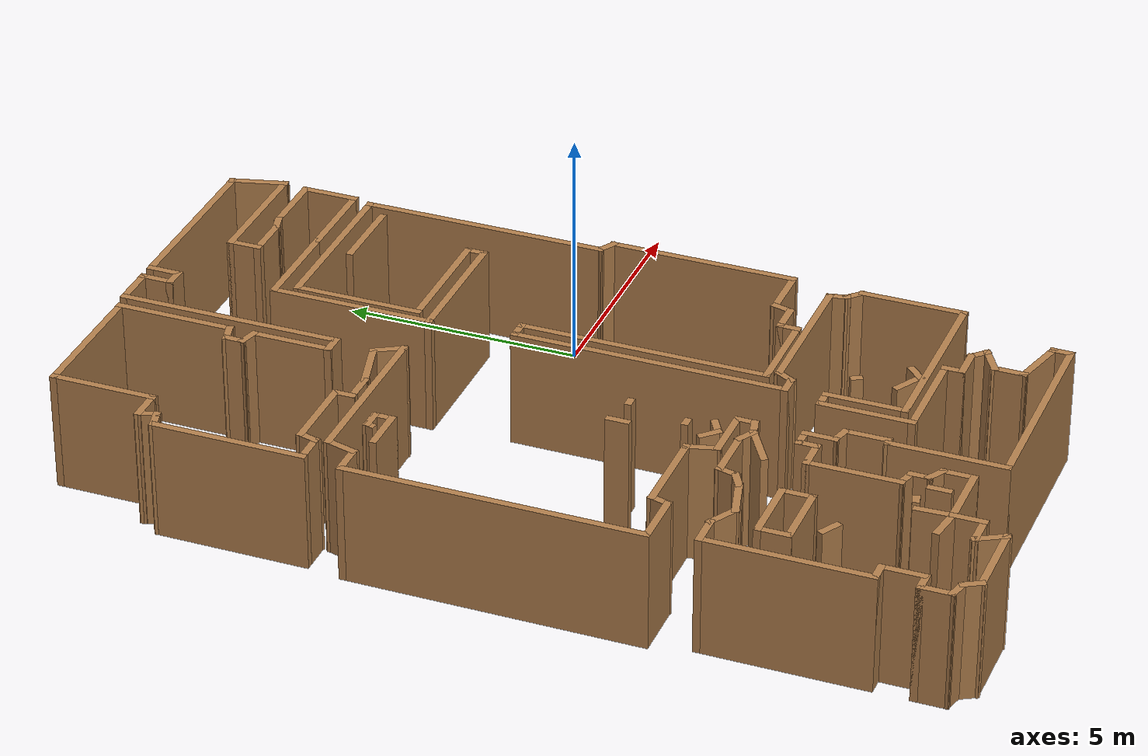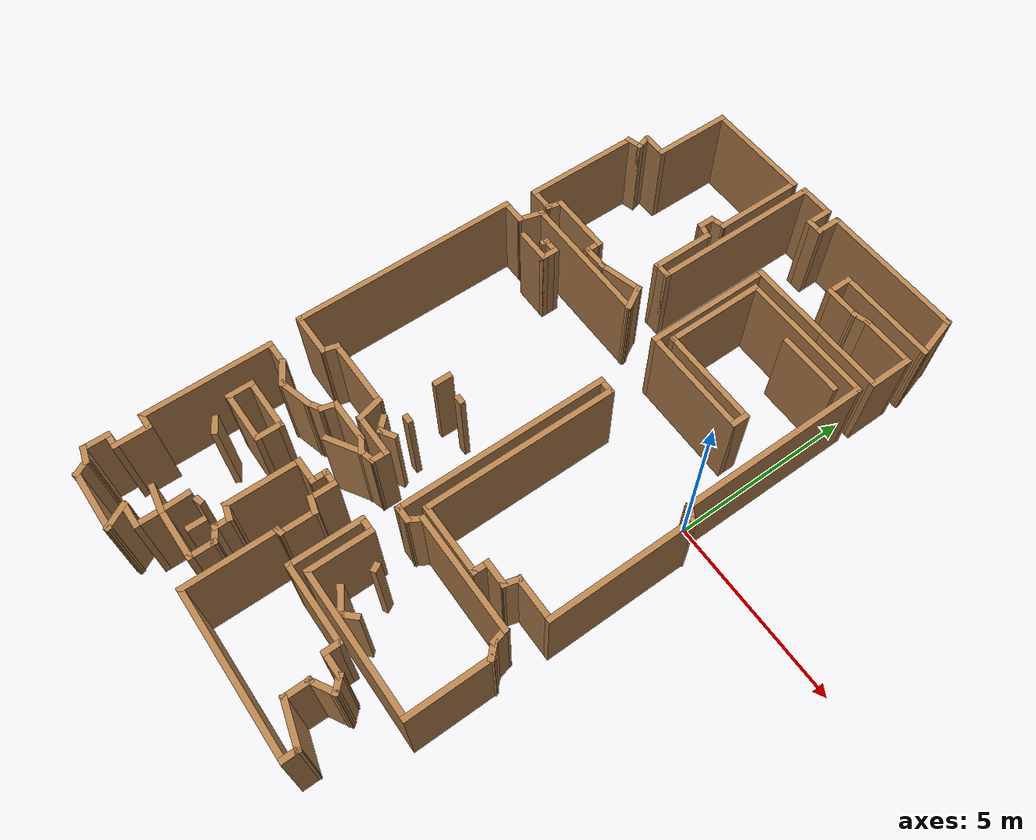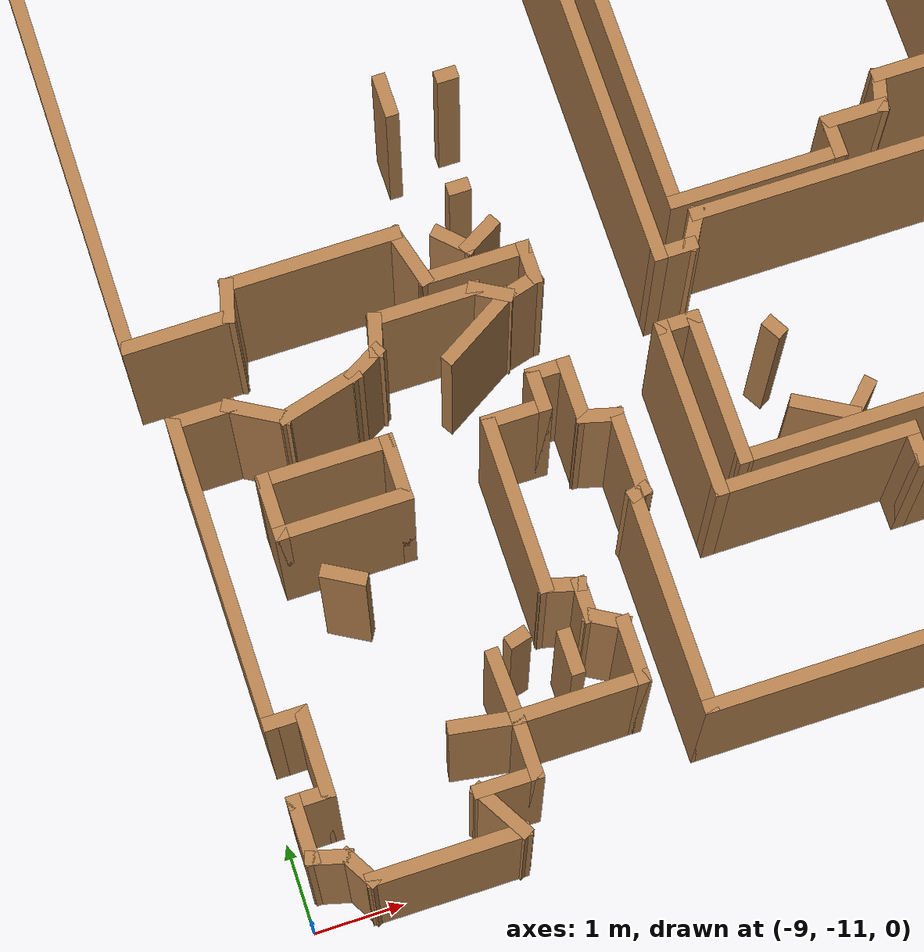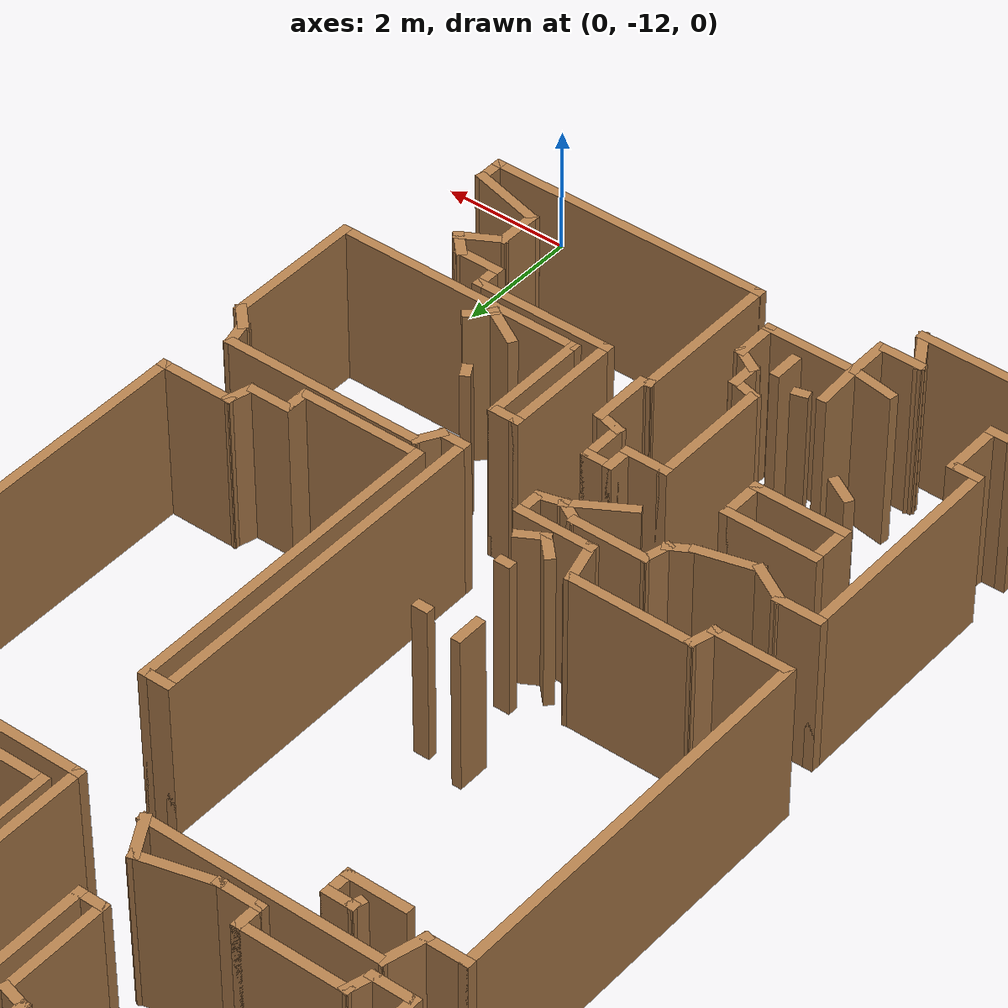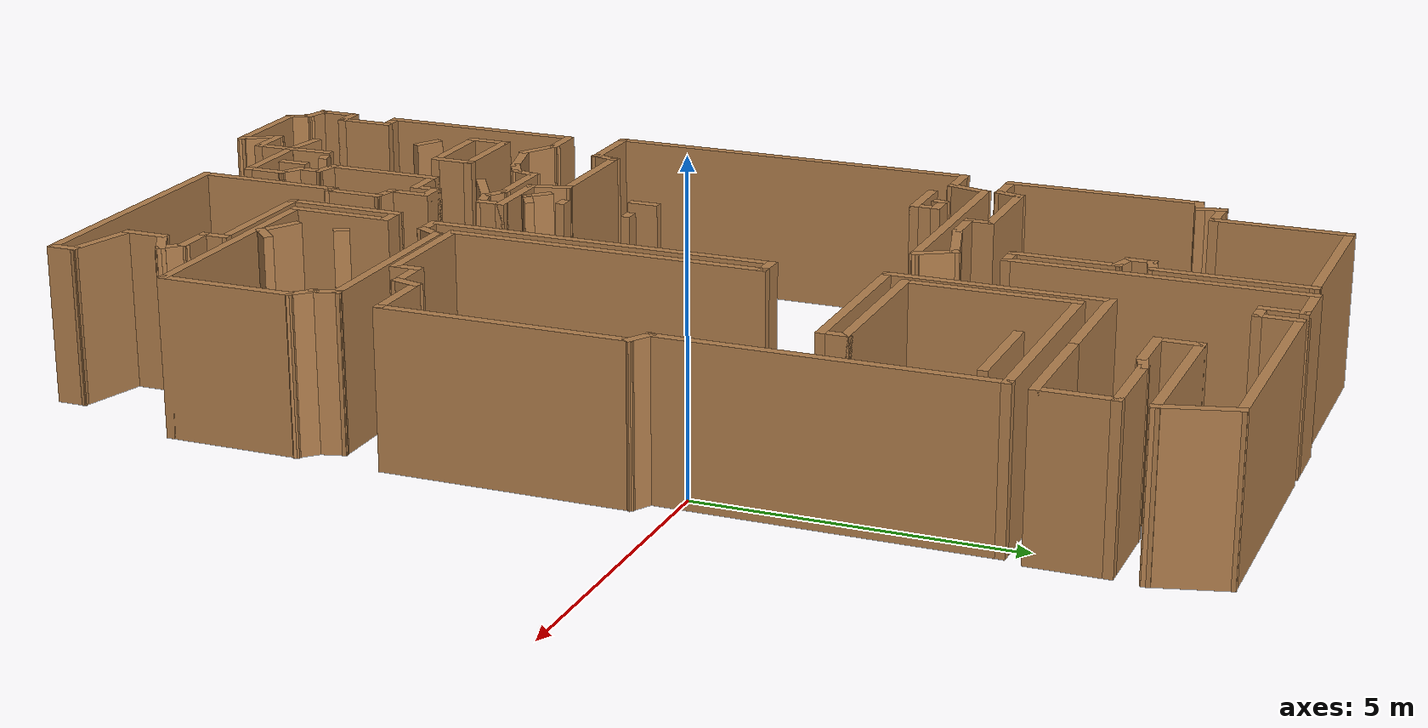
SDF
<?xml version='1.0'?>
<sdf version='1.6'>
  <model name='map_31'>
    <pose frame=''>-4.20908 -1.66774 0 0 -0 0</pose>
    <link name='Wall_0'>
      <collision name='Wall_0_Collision'>
        <geometry>
          <box>
            <size>3 0.15 2.5</size>
          </box>
        </geometry>
        <pose frame=''>0 0 1.25 0 -0 0</pose>
      </collision>
      <visual name='Wall_0_Visual'>
        <pose frame=''>0 0 1.25 0 -0 0</pose>
        <geometry>
          <box>
            <size>3 0.15 2.5</size>
          </box>
        </geometry>
        <material>
          <script>
            <uri>file://media/materials/scripts/gazebo.material</uri>
            <name>Gazebo/Wood</name>
          </script>
          <ambient>1 1 1 1</ambient>
        </material>
        <meta>
          <layer>0</layer>
        </meta>
      </visual>
      <pose frame=''>-2.44947 9.31 0 0 -0 3.14159</pose>
    </link>
    <link name='Wall_1'>
      <collision name='Wall_1_Collision'>
        <geometry>
          <box>
            <size>2.25 0.15 2.5</size>
          </box>
        </geometry>
        <pose frame=''>0 0 1.25 0 -0 0</pose>
      </collision>
      <visual name='Wall_1_Visual'>
        <pose frame=''>0 0 1.25 0 -0 0</pose>
        <geometry>
          <box>
            <size>2.25 0.15 2.5</size>
          </box>
        </geometry>
        <material>
          <script>
            <uri>file://media/materials/scripts/gazebo.material</uri>
            <name>Gazebo/Wood</name>
          </script>
          <ambient>1 1 1 1</ambient>
        </material>
        <meta>
          <layer>0</layer>
        </meta>
      </visual>
      <pose frame=''>-3.87447 8.26 0 0 -0 -1.5708</pose>
    </link>
    <link name='Wall_10'>
      <collision name='Wall_10_Collision'>
        <geometry>
          <box>
            <size>0.75 0.15 2.5</size>
          </box>
        </geometry>
        <pose frame=''>0 0 1.25 0 -0 0</pose>
      </collision>
      <visual name='Wall_10_Visual'>
        <pose frame=''>0 0 1.25 0 -0 0</pose>
        <geometry>
          <box>
            <size>0.75 0.15 2.5</size>
          </box>
        </geometry>
        <material>
          <script>
            <uri>file://media/materials/scripts/gazebo.material</uri>
            <name>Gazebo/Wood</name>
          </script>
          <ambient>1 1 1 1</ambient>
        </material>
        <meta>
          <layer>0</layer>
        </meta>
      </visual>
      <pose frame=''>-2.13137 3.66941 0 0 -0 0</pose>
    </link>
    <link name='Wall_100'>
      <collision name='Wall_100_Collision'>
        <geometry>
          <box>
            <size>3.5 0.15 2.5</size>
          </box>
        </geometry>
        <pose frame=''>0 0 1.25 0 -0 0</pose>
      </collision>
      <visual name='Wall_100_Visual'>
        <pose frame=''>0 0 1.25 0 -0 0</pose>
        <geometry>
          <box>
            <size>3.5 0.15 2.5</size>
          </box>
        </geometry>
        <material>
          <script>
            <uri>file://media/materials/scripts/gazebo.material</uri>
            <name>Gazebo/Wood</name>
          </script>
          <ambient>1 1 1 1</ambient>
        </material>
        <meta>
          <layer>0</layer>
        </meta>
      </visual>
      <pose frame=''>0.643586 5.04256 0 0 -0 1.5708</pose>
    </link>
    <link name='Wall_101'>
      <collision name='Wall_101_Collision'>
        <geometry>
          <box>
            <size>2.25 0.15 2.5</size>
          </box>
        </geometry>
        <pose frame=''>0 0 1.25 0 -0 0</pose>
      </collision>
      <visual name='Wall_101_Visual'>
        <pose frame=''>0 0 1.25 0 -0 0</pose>
        <geometry>
          <box>
            <size>2.25 0.15 2.5</size>
          </box>
        </geometry>
        <material>
          <script>
            <uri>file://media/materials/scripts/gazebo.material</uri>
            <name>Gazebo/Wood</name>
          </script>
          <ambient>1 1 1 1</ambient>
        </material>
        <meta>
          <layer>0</layer>
        </meta>
      </visual>
      <pose frame=''>1.69359 6.71756 0 0 -0 0</pose>
    </link>
    <link name='Wall_102'>
      <collision name='Wall_102_Collision'>
        <geometry>
          <box>
            <size>2 0.15 2.5</size>
          </box>
        </geometry>
        <pose frame=''>0 0 1.25 0 -0 0</pose>
      </collision>
      <visual name='Wall_102_Visual'>
        <pose frame=''>0 0 1.25 0 -0 0</pose>
        <geometry>
          <box>
            <size>2 0.15 2.5</size>
          </box>
        </geometry>
        <material>
          <script>
            <uri>file://media/materials/scripts/gazebo.material</uri>
            <name>Gazebo/Wood</name>
          </script>
          <ambient>1 1 1 1</ambient>
        </material>
        <meta>
          <layer>0</layer>
        </meta>
      </visual>
      <pose frame=''>3.66859 6.71756 0 0 -0 0</pose>
    </link>
    <link name='Wall_103'>
      <collision name='Wall_103_Collision'>
        <geometry>
          <box>
            <size>1.25 0.15 2.5</size>
          </box>
        </geometry>
        <pose frame=''>0 0 1.25 0 -0 0</pose>
      </collision>
      <visual name='Wall_103_Visual'>
        <pose frame=''>0 0 1.25 0 -0 0</pose>
        <geometry>
          <box>
            <size>1.25 0.15 2.5</size>
          </box>
        </geometry>
        <material>
          <script>
            <uri>file://media/materials/scripts/gazebo.material</uri>
            <name>Gazebo/Wood</name>
          </script>
          <ambient>1 1 1 1</ambient>
        </material>
        <meta>
          <layer>0</layer>
        </meta>
      </visual>
      <pose frame=''>4.59359 7.26756 0 0 -0 1.5708</pose>
    </link>
    <link name='Wall_104'>
      <collision name='Wall_104_Collision'>
        <geometry>
          <box>
            <size>1.5 0.15 2.5</size>
          </box>
        </geometry>
        <pose frame=''>0 0 1.25 0 -0 0</pose>
      </collision>
      <visual name='Wall_104_Visual'>
        <pose frame=''>0 0 1.25 0 -0 0</pose>
        <geometry>
          <box>
            <size>1.5 0.15 2.5</size>
          </box>
        </geometry>
        <material>
          <script>
            <uri>file://media/materials/scripts/gazebo.material</uri>
            <name>Gazebo/Wood</name>
          </script>
          <ambient>1 1 1 1</ambient>
        </material>
        <meta>
          <layer>0</layer>
        </meta>
      </visual>
      <pose frame=''>3.91859 7.81756 0 0 -0 3.14159</pose>
    </link>
    <link name='Wall_105'>
      <collision name='Wall_105_Collision'>
        <geometry>
          <box>
            <size>0.5 0.15 2.5</size>
          </box>
        </geometry>
        <pose frame=''>0 0 1.25 0 -0 0</pose>
      </collision>
      <visual name='Wall_105_Visual'>
        <pose frame=''>0 0 1.25 0 -0 0</pose>
        <geometry>
          <box>
            <size>0.5 0.15 2.5</size>
          </box>
        </geometry>
        <material>
          <script>
            <uri>file://media/materials/scripts/gazebo.material</uri>
            <name>Gazebo/Wood</name>
          </script>
          <ambient>1 1 1 1</ambient>
        </material>
        <meta>
          <layer>0</layer>
        </meta>
      </visual>
      <pose frame=''>3.07455 7.77226 0 0 -0 -2.87979</pose>
    </link>
    <link name='Wall_106'>
      <collision name='Wall_106_Collision'>
        <geometry>
          <box>
            <size>1 0.15 2.5</size>
          </box>
        </geometry>
        <pose frame=''>0 0 1.25 0 -0 0</pose>
      </collision>
      <visual name='Wall_106_Visual'>
        <pose frame=''>0 0 1.25 0 -0 0</pose>
        <geometry>
          <box>
            <size>1 0.15 2.5</size>
          </box>
        </geometry>
        <material>
          <script>
            <uri>file://media/materials/scripts/gazebo.material</uri>
            <name>Gazebo/Wood</name>
          </script>
          <ambient>1 1 1 1</ambient>
        </material>
        <meta>
          <layer>0</layer>
        </meta>
      </visual>
      <pose frame=''>2.48051 7.72697 0 0 -0 3.14159</pose>
    </link>
    <link name='Wall_107'>
      <collision name='Wall_107_Collision'>
        <geometry>
          <box>
            <size>0.75 0.15 2.5</size>
          </box>
        </geometry>
        <pose frame=''>0 0 1.25 0 -0 0</pose>
      </collision>
      <visual name='Wall_107_Visual'>
        <pose frame=''>0 0 1.25 0 -0 0</pose>
        <geometry>
          <box>
            <size>0.75 0.15 2.5</size>
          </box>
        </geometry>
        <material>
          <script>
            <uri>file://media/materials/scripts/gazebo.material</uri>
            <name>Gazebo/Wood</name>
          </script>
          <ambient>1 1 1 1</ambient>
        </material>
        <meta>
          <layer>0</layer>
        </meta>
      </visual>
      <pose frame=''>2.05551 8.02697 0 0 -0 1.5708</pose>
    </link>
    <link name='Wall_108'>
      <collision name='Wall_108_Collision'>
        <geometry>
          <box>
            <size>2.75 0.15 2.5</size>
          </box>
        </geometry>
        <pose frame=''>0 0 1.25 0 -0 0</pose>
      </collision>
      <visual name='Wall_108_Visual'>
        <pose frame=''>0 0 1.25 0 -0 0</pose>
        <geometry>
          <box>
            <size>2.75 0.15 2.5</size>
          </box>
        </geometry>
        <material>
          <script>
            <uri>file://media/materials/scripts/gazebo.material</uri>
            <name>Gazebo/Wood</name>
          </script>
          <ambient>1 1 1 1</ambient>
        </material>
        <meta>
          <layer>0</layer>
        </meta>
      </visual>
      <pose frame=''>3.35551 8.32697 0 0 -0 0</pose>
    </link>
    <link name='Wall_109'>
      <collision name='Wall_109_Collision'>
        <geometry>
          <box>
            <size>1.25 0.15 2.5</size>
          </box>
        </geometry>
        <pose frame=''>0 0 1.25 0 -0 0</pose>
      </collision>
      <visual name='Wall_109_Visual'>
        <pose frame=''>0 0 1.25 0 -0 0</pose>
        <geometry>
          <box>
            <size>1.25 0.15 2.5</size>
          </box>
        </geometry>
        <material>
          <script>
            <uri>file://media/materials/scripts/gazebo.material</uri>
            <name>Gazebo/Wood</name>
          </script>
          <ambient>1 1 1 1</ambient>
        </material>
        <meta>
          <layer>0</layer>
        </meta>
      </visual>
      <pose frame=''>4.51316 8.85823 0 0 -0 1.8326</pose>
    </link>
    <link name='Wall_11'>
      <collision name='Wall_11_Collision'>
        <geometry>
          <box>
            <size>1.25 0.15 2.5</size>
          </box>
        </geometry>
        <pose frame=''>0 0 1.25 0 -0 0</pose>
      </collision>
      <visual name='Wall_11_Visual'>
        <pose frame=''>0 0 1.25 0 -0 0</pose>
        <geometry>
          <box>
            <size>1.25 0.15 2.5</size>
          </box>
        </geometry>
        <material>
          <script>
            <uri>file://media/materials/scripts/gazebo.material</uri>
            <name>Gazebo/Wood</name>
          </script>
          <ambient>1 1 1 1</ambient>
        </material>
        <meta>
          <layer>0</layer>
        </meta>
      </visual>
      <pose frame=''>-1.30011 3.81176 0 0 -0 0.261799</pose>
    </link>
    <link name='Wall_110'>
      <collision name='Wall_110_Collision'>
        <geometry>
          <box>
            <size>4 0.15 2.5</size>
          </box>
        </geometry>
        <pose frame=''>0 0 1.25 0 -0 0</pose>
      </collision>
      <visual name='Wall_110_Visual'>
        <pose frame=''>0 0 1.25 0 -0 0</pose>
        <geometry>
          <box>
            <size>4 0.15 2.5</size>
          </box>
        </geometry>
        <material>
          <script>
            <uri>file://media/materials/scripts/gazebo.material</uri>
            <name>Gazebo/Wood</name>
          </script>
          <ambient>1 1 1 1</ambient>
        </material>
        <meta>
          <layer>0</layer>
        </meta>
      </visual>
      <pose frame=''>2.44581 9.38949 0 0 -0 3.14159</pose>
    </link>
    <link name='Wall_111'>
      <collision name='Wall_111_Collision'>
        <geometry>
          <box>
            <size>0.75 0.15 2.5</size>
          </box>
        </geometry>
        <pose frame=''>0 0 1.25 0 -0 0</pose>
      </collision>
      <visual name='Wall_111_Visual'>
        <pose frame=''>0 0 1.25 0 -0 0</pose>
        <geometry>
          <box>
            <size>0.75 0.15 2.5</size>
          </box>
        </geometry>
        <material>
          <script>
            <uri>file://media/materials/scripts/gazebo.material</uri>
            <name>Gazebo/Wood</name>
          </script>
          <ambient>1 1 1 1</ambient>
        </material>
        <meta>
          <layer>0</layer>
        </meta>
      </visual>
      <pose frame=''>0.520811 9.08949 0 0 -0 -1.5708</pose>
    </link>
    <link name='Wall_112'>
      <collision name='Wall_112_Collision'>
        <geometry>
          <box>
            <size>0.5 0.15 2.5</size>
          </box>
        </geometry>
        <pose frame=''>0 0 1.25 0 -0 0</pose>
      </collision>
      <visual name='Wall_112_Visual'>
        <pose frame=''>0 0 1.25 0 -0 0</pose>
        <geometry>
          <box>
            <size>0.5 0.15 2.5</size>
          </box>
        </geometry>
        <material>
          <script>
            <uri>file://media/materials/scripts/gazebo.material</uri>
            <name>Gazebo/Wood</name>
          </script>
          <ambient>1 1 1 1</ambient>
        </material>
        <meta>
          <layer>0</layer>
        </meta>
      </visual>
      <pose frame=''>0.345811 8.78949 0 0 -0 3.14159</pose>
    </link>
    <link name='Wall_113'>
      <collision name='Wall_113_Collision'>
        <geometry>
          <box>
            <size>0.75 0.15 2.5</size>
          </box>
        </geometry>
        <pose frame=''>0 0 1.25 0 -0 0</pose>
      </collision>
      <visual name='Wall_113_Visual'>
        <pose frame=''>0 0 1.25 0 -0 0</pose>
        <geometry>
          <box>
            <size>0.75 0.15 2.5</size>
          </box>
        </geometry>
        <material>
          <script>
            <uri>file://media/materials/scripts/gazebo.material</uri>
            <name>Gazebo/Wood</name>
          </script>
          <ambient>1 1 1 1</ambient>
        </material>
        <meta>
          <layer>0</layer>
        </meta>
      </visual>
      <pose frame=''>0.170811 9.08949 0 0 -0 1.5708</pose>
    </link>
    <link name='Wall_116'>
      <collision name='Wall_116_Collision'>
        <geometry>
          <box>
            <size>1 0.15 2.5</size>
          </box>
        </geometry>
        <pose frame=''>0 0 1.25 0 -0 0</pose>
      </collision>
      <visual name='Wall_116_Visual'>
        <pose frame=''>0 0 1.25 0 -0 0</pose>
        <geometry>
          <box>
            <size>1 0.15 2.5</size>
          </box>
        </geometry>
        <material>
          <script>
            <uri>file://media/materials/scripts/gazebo.material</uri>
            <name>Gazebo/Wood</name>
          </script>
          <ambient>1 1 1 1</ambient>
        </material>
        <meta>
          <layer>0</layer>
        </meta>
      </visual>
      <pose frame=''>-0.254189 9.38949 0 0 -0 3.14159</pose>
    </link>
    <link name='Wall_117'>
      <collision name='Wall_117_Collision'>
        <geometry>
          <box>
            <size>4.75 0.15 2.5</size>
          </box>
        </geometry>
        <pose frame=''>0 0 1.25 0 -0 0</pose>
      </collision>
      <visual name='Wall_117_Visual'>
        <pose frame=''>0 0 1.25 0 -0 0</pose>
        <geometry>
          <box>
            <size>4.75 0.15 2.5</size>
          </box>
        </geometry>
        <material>
          <script>
            <uri>file://media/materials/scripts/gazebo.material</uri>
            <name>Gazebo/Wood</name>
          </script>
          <ambient>1 1 1 1</ambient>
        </material>
        <meta>
          <layer>0</layer>
        </meta>
      </visual>
      <pose frame=''>-0.679188 7.08949 0 0 -0 -1.5708</pose>
    </link>
    <link name='Wall_12'>
      <collision name='Wall_12_Collision'>
        <geometry>
          <box>
            <size>0.75 0.15 2.5</size>
          </box>
        </geometry>
        <pose frame=''>0 0 1.25 0 -0 0</pose>
      </collision>
      <visual name='Wall_12_Visual'>
        <pose frame=''>0 0 1.25 0 -0 0</pose>
        <geometry>
          <box>
            <size>0.75 0.15 2.5</size>
          </box>
        </geometry>
        <material>
          <script>
            <uri>file://media/materials/scripts/gazebo.material</uri>
            <name>Gazebo/Wood</name>
          </script>
          <ambient>1 1 1 1</ambient>
        </material>
        <meta>
          <layer>0</layer>
        </meta>
      </visual>
      <pose frame=''>-0.618855 3.6943 0 0 -0 -1.0472</pose>
    </link>
    <link name='Wall_120'>
      <collision name='Wall_120_Collision'>
        <geometry>
          <box>
            <size>0.5 0.15 2.5</size>
          </box>
        </geometry>
        <pose frame=''>0 0 1.25 0 -0 0</pose>
      </collision>
      <visual name='Wall_120_Visual'>
        <pose frame=''>0 0 1.25 0 -0 0</pose>
        <geometry>
          <box>
            <size>0.5 0.15 2.5</size>
          </box>
        </geometry>
        <material>
          <script>
            <uri>file://media/materials/scripts/gazebo.material</uri>
            <name>Gazebo/Wood</name>
          </script>
          <ambient>1 1 1 1</ambient>
        </material>
        <meta>
          <layer>0</layer>
        </meta>
      </visual>
      <pose frame=''>-0.854189 4.78949 0 0 -0 3.14159</pose>
    </link>
    <link name='Wall_124'>
      <collision name='Wall_124_Collision'>
        <geometry>
          <box>
            <size>1.75 0.15 2.5</size>
          </box>
        </geometry>
        <pose frame=''>0 0 1.25 0 -0 0</pose>
      </collision>
      <visual name='Wall_124_Visual'>
        <pose frame=''>0 0 1.25 0 -0 0</pose>
        <geometry>
          <box>
            <size>1.75 0.15 2.5</size>
          </box>
        </geometry>
        <material>
          <script>
            <uri>file://media/materials/scripts/gazebo.material</uri>
            <name>Gazebo/Wood</name>
          </script>
          <ambient>1 1 1 1</ambient>
        </material>
        <meta>
          <layer>0</layer>
        </meta>
      </visual>
      <pose frame=''>-1.02919 5.58949 0 0 -0 1.5708</pose>
    </link>
    <link name='Wall_125'>
      <collision name='Wall_125_Collision'>
        <geometry>
          <box>
            <size>0.5 0.15 2.5</size>
          </box>
        </geometry>
        <pose frame=''>0 0 1.25 0 -0 0</pose>
      </collision>
      <visual name='Wall_125_Visual'>
        <pose frame=''>0 0 1.25 0 -0 0</pose>
        <geometry>
          <box>
            <size>0.5 0.15 2.5</size>
          </box>
        </geometry>
        <material>
          <script>
            <uri>file://media/materials/scripts/gazebo.material</uri>
            <name>Gazebo/Wood</name>
          </script>
          <ambient>1 1 1 1</ambient>
        </material>
        <meta>
          <layer>0</layer>
        </meta>
      </visual>
      <pose frame=''>-1.19823 6.43478 0 0 -0 2.87979</pose>
    </link>
    <link name='Wall_126'>
      <collision name='Wall_126_Collision'>
        <geometry>
          <box>
            <size>0.5 0.15 2.5</size>
          </box>
        </geometry>
        <pose frame=''>0 0 1.25 0 -0 0</pose>
      </collision>
      <visual name='Wall_126_Visual'>
        <pose frame=''>0 0 1.25 0 -0 0</pose>
        <geometry>
          <box>
            <size>0.5 0.15 2.5</size>
          </box>
        </geometry>
        <material>
          <script>
            <uri>file://media/materials/scripts/gazebo.material</uri>
            <name>Gazebo/Wood</name>
          </script>
          <ambient>1 1 1 1</ambient>
        </material>
        <meta>
          <layer>0</layer>
        </meta>
      </visual>
      <pose frame=''>-1.36726 6.65508 0 0 -0 1.5708</pose>
    </link>
    <link name='Wall_127'>
      <collision name='Wall_127_Collision'>
        <geometry>
          <box>
            <size>0.5 0.15 2.5</size>
          </box>
        </geometry>
        <pose frame=''>0 0 1.25 0 -0 0</pose>
      </collision>
      <visual name='Wall_127_Visual'>
        <pose frame=''>0 0 1.25 0 -0 0</pose>
        <geometry>
          <box>
            <size>0.5 0.15 2.5</size>
          </box>
        </geometry>
        <material>
          <script>
            <uri>file://media/materials/scripts/gazebo.material</uri>
            <name>Gazebo/Wood</name>
          </script>
          <ambient>1 1 1 1</ambient>
        </material>
        <meta>
          <layer>0</layer>
        </meta>
      </visual>
      <pose frame=''>-1.19823 6.87537 0 0 -0 0.261799</pose>
    </link>
    <link name='Wall_128'>
      <collision name='Wall_128_Collision'>
        <geometry>
          <box>
            <size>2.53934 0.15 2.5</size>
          </box>
        </geometry>
        <pose frame=''>0 0 1.25 0 -0 0</pose>
      </collision>
      <visual name='Wall_128_Visual'>
        <pose frame=''>0 0 1.25 0 -0 0</pose>
        <geometry>
          <box>
            <size>2.53934 0.15 2.5</size>
          </box>
        </geometry>
        <material>
          <script>
            <uri>file://media/materials/scripts/gazebo.material</uri>
            <name>Gazebo/Wood</name>
          </script>
          <ambient>1 1 1 1</ambient>
        </material>
        <meta>
          <layer>0</layer>
        </meta>
      </visual>
      <pose frame=''>-1.02683 8.11533 0 0 -0 1.56882</pose>
    </link>
    <link name='Wall_13'>
      <collision name='Wall_13_Collision'>
        <geometry>
          <box>
            <size>3.75 0.15 2.5</size>
          </box>
        </geometry>
        <pose frame=''>0 0 1.25 0 -0 0</pose>
      </collision>
      <visual name='Wall_13_Visual'>
        <pose frame=''>0 0 1.25 0 -0 0</pose>
        <geometry>
          <box>
            <size>3.75 0.15 2.5</size>
          </box>
        </geometry>
        <material>
          <script>
            <uri>file://media/materials/scripts/gazebo.material</uri>
            <name>Gazebo/Wood</name>
          </script>
          <ambient>1 1 1 1</ambient>
        </material>
        <meta>
          <layer>0</layer>
        </meta>
      </visual>
      <pose frame=''>-2.26885 3.4345 0 0 -0 3.14159</pose>
    </link>
    <link name='Wall_130'>
      <collision name='Wall_130_Collision'>
        <geometry>
          <box>
            <size>1.75 0.15 2.5</size>
          </box>
        </geometry>
        <pose frame=''>0 0 1.25 0 -0 0</pose>
      </collision>
      <visual name='Wall_130_Visual'>
        <pose frame=''>0 0 1.25 0 -0 0</pose>
        <geometry>
          <box>
            <size>1.75 0.15 2.5</size>
          </box>
        </geometry>
        <material>
          <script>
            <uri>file://media/materials/scripts/gazebo.material</uri>
            <name>Gazebo/Wood</name>
          </script>
          <ambient>1 1 1 1</ambient>
        </material>
        <meta>
          <layer>0</layer>
        </meta>
      </visual>
      <pose frame=''>3.32399 5.88389 0 0 -0 0</pose>
    </link>
    <link name='Wall_132'>
      <collision name='Wall_132_Collision'>
        <geometry>
          <box>
            <size>0.5 0.15 2.5</size>
          </box>
        </geometry>
        <pose frame=''>0 0 1.25 0 -0 0</pose>
      </collision>
      <visual name='Wall_132_Visual'>
        <pose frame=''>0 0 1.25 0 -0 0</pose>
        <geometry>
          <box>
            <size>0.5 0.15 2.5</size>
          </box>
        </geometry>
        <material>
          <script>
            <uri>file://media/materials/scripts/gazebo.material</uri>
            <name>Gazebo/Wood</name>
          </script>
          <ambient>1 1 1 1</ambient>
        </material>
        <meta>
          <layer>0</layer>
        </meta>
      </visual>
      <pose frame=''>-1.39156 -1.38804 0 0 -0 -1.5708</pose>
    </link>
    <link name='Wall_134'>
      <collision name='Wall_134_Collision'>
        <geometry>
          <box>
            <size>0.25 0.15 2.5</size>
          </box>
        </geometry>
        <pose frame=''>0 0 1.25 0 -0 0</pose>
      </collision>
      <visual name='Wall_134_Visual'>
        <pose frame=''>0 0 1.25 0 -0 0</pose>
        <geometry>
          <box>
            <size>0.25 0.15 2.5</size>
          </box>
        </geometry>
        <material>
          <script>
            <uri>file://media/materials/scripts/gazebo.material</uri>
            <name>Gazebo/Wood</name>
          </script>
          <ambient>1 1 1 1</ambient>
        </material>
        <meta>
          <layer>0</layer>
        </meta>
      </visual>
      <pose frame=''>-0.699161 -1.36599 0 0 -0 0</pose>
    </link>
    <link name='Wall_136'>
      <collision name='Wall_136_Collision'>
        <geometry>
          <box>
            <size>0.25 0.15 2.5</size>
          </box>
        </geometry>
        <pose frame=''>0 0 1.25 0 -0 0</pose>
      </collision>
      <visual name='Wall_136_Visual'>
        <pose frame=''>0 0 1.25 0 -0 0</pose>
        <geometry>
          <box>
            <size>0.25 0.15 2.5</size>
          </box>
        </geometry>
        <material>
          <script>
            <uri>file://media/materials/scripts/gazebo.material</uri>
            <name>Gazebo/Wood</name>
          </script>
          <ambient>1 1 1 1</ambient>
        </material>
        <meta>
          <layer>0</layer>
        </meta>
      </visual>
      <pose frame=''>-0.974473 -2.62019 0 0 -0 0</pose>
    </link>
    <link name='Wall_138'>
      <collision name='Wall_138_Collision'>
        <geometry>
          <box>
            <size>0.5 0.15 2.5</size>
          </box>
        </geometry>
        <pose frame=''>0 0 1.25 0 -0 0</pose>
      </collision>
      <visual name='Wall_138_Visual'>
        <pose frame=''>0 0 1.25 0 -0 0</pose>
        <geometry>
          <box>
            <size>0.5 0.15 2.5</size>
          </box>
        </geometry>
        <material>
          <script>
            <uri>file://media/materials/scripts/gazebo.material</uri>
            <name>Gazebo/Wood</name>
          </script>
          <ambient>1 1 1 1</ambient>
        </material>
        <meta>
          <layer>0</layer>
        </meta>
      </visual>
      <pose frame=''>-1.20663 -3.1722 0 0 -0 -0.785398</pose>
    </link>
    <link name='Wall_139'>
      <collision name='Wall_139_Collision'>
        <geometry>
          <box>
            <size>0.5 0.15 2.5</size>
          </box>
        </geometry>
        <pose frame=''>0 0 1.25 0 -0 0</pose>
      </collision>
      <visual name='Wall_139_Visual'>
        <pose frame=''>0 0 1.25 0 -0 0</pose>
        <geometry>
          <box>
            <size>0.5 0.15 2.5</size>
          </box>
        </geometry>
        <material>
          <script>
            <uri>file://media/materials/scripts/gazebo.material</uri>
            <name>Gazebo/Wood</name>
          </script>
          <ambient>1 1 1 1</ambient>
        </material>
        <meta>
          <layer>0</layer>
        </meta>
      </visual>
      <pose frame=''>-0.931333 -3.20844 0 0 -0 0.523599</pose>
    </link>
    <link name='Wall_14'>
      <collision name='Wall_14_Collision'>
        <geometry>
          <box>
            <size>0.75 0.15 2.5</size>
          </box>
        </geometry>
        <pose frame=''>0 0 1.25 0 -0 0</pose>
      </collision>
      <visual name='Wall_14_Visual'>
        <pose frame=''>0 0 1.25 0 -0 0</pose>
        <geometry>
          <box>
            <size>0.75 0.15 2.5</size>
          </box>
        </geometry>
        <material>
          <script>
            <uri>file://media/materials/scripts/gazebo.material</uri>
            <name>Gazebo/Wood</name>
          </script>
          <ambient>1 1 1 1</ambient>
        </material>
        <meta>
          <layer>0</layer>
        </meta>
      </visual>
      <pose frame=''>-4.1465 3.14472 0 0 -0 -1.8326</pose>
    </link>
    <link name='Wall_141'>
      <collision name='Wall_141_Collision'>
        <geometry>
          <box>
            <size>1 0.15 2.5</size>
          </box>
        </geometry>
        <pose frame=''>0 0 1.25 0 -0 0</pose>
      </collision>
      <visual name='Wall_141_Visual'>
        <pose frame=''>0 0 1.25 0 -0 0</pose>
        <geometry>
          <box>
            <size>1 0.15 2.5</size>
          </box>
        </geometry>
        <material>
          <script>
            <uri>file://media/materials/scripts/gazebo.material</uri>
            <name>Gazebo/Wood</name>
          </script>
          <ambient>1 1 1 1</ambient>
        </material>
        <meta>
          <layer>0</layer>
        </meta>
      </visual>
      <pose frame=''>-3.322 2.64133 0 0 -0 0</pose>
    </link>
    <link name='Wall_142'>
      <collision name='Wall_142_Collision'>
        <geometry>
          <box>
            <size>0.5 0.15 2.5</size>
          </box>
        </geometry>
        <pose frame=''>0 0 1.25 0 -0 0</pose>
      </collision>
      <visual name='Wall_142_Visual'>
        <pose frame=''>0 0 1.25 0 -0 0</pose>
        <geometry>
          <box>
            <size>0.5 0.15 2.5</size>
          </box>
        </geometry>
        <material>
          <script>
            <uri>file://media/materials/scripts/gazebo.material</uri>
            <name>Gazebo/Wood</name>
          </script>
          <ambient>1 1 1 1</ambient>
        </material>
        <meta>
          <layer>0</layer>
        </meta>
      </visual>
      <pose frame=''>-2.897 2.81633 0 0 -0 1.5708</pose>
    </link>
    <link name='Wall_143'>
      <collision name='Wall_143_Collision'>
        <geometry>
          <box>
            <size>0.5 0.15 2.5</size>
          </box>
        </geometry>
        <pose frame=''>0 0 1.25 0 -0 0</pose>
      </collision>
      <visual name='Wall_143_Visual'>
        <pose frame=''>0 0 1.25 0 -0 0</pose>
        <geometry>
          <box>
            <size>0.5 0.15 2.5</size>
          </box>
        </geometry>
        <material>
          <script>
            <uri>file://media/materials/scripts/gazebo.material</uri>
            <name>Gazebo/Wood</name>
          </script>
          <ambient>1 1 1 1</ambient>
        </material>
        <meta>
          <layer>0</layer>
        </meta>
      </visual>
      <pose frame=''>-3.072 2.99133 0 0 -0 3.14159</pose>
    </link>
    <link name='Wall_144'>
      <collision name='Wall_144_Collision'>
        <geometry>
          <box>
            <size>0.25 0.15 2.5</size>
          </box>
        </geometry>
        <pose frame=''>0 0 1.25 0 -0 0</pose>
      </collision>
      <visual name='Wall_144_Visual'>
        <pose frame=''>0 0 1.25 0 -0 0</pose>
        <geometry>
          <box>
            <size>0.25 0.15 2.5</size>
          </box>
        </geometry>
        <material>
          <script>
            <uri>file://media/materials/scripts/gazebo.material</uri>
            <name>Gazebo/Wood</name>
          </script>
          <ambient>1 1 1 1</ambient>
        </material>
        <meta>
          <layer>0</layer>
        </meta>
      </visual>
      <pose frame=''>-3.25994 2.94303 0 0 -0 -1.8326</pose>
    </link>
    <link name='Wall_146'>
      <collision name='Wall_146_Collision'>
        <geometry>
          <box>
            <size>1.05065 0.15 2.5</size>
          </box>
        </geometry>
        <pose frame=''>0 0 1.25 0 -0 0</pose>
      </collision>
      <visual name='Wall_146_Visual'>
        <pose frame=''>0 0 1.25 0 -0 0</pose>
        <geometry>
          <box>
            <size>1.05065 0.15 2.5</size>
          </box>
        </geometry>
        <material>
          <script>
            <uri>file://media/materials/scripts/gazebo.material</uri>
            <name>Gazebo/Wood</name>
          </script>
          <ambient>1 1 1 1</ambient>
        </material>
        <meta>
          <layer>0</layer>
        </meta>
      </visual>
      <pose frame=''>-1.25131 -4.16078 0 0 -0 0.545501</pose>
    </link>
    <link name='Wall_148'>
      <collision name='Wall_148_Collision'>
        <geometry>
          <box>
            <size>0.796706 0.15 2.5</size>
          </box>
        </geometry>
        <pose frame=''>0 0 1.25 0 -0 0</pose>
      </collision>
      <visual name='Wall_148_Visual'>
        <pose frame=''>0 0 1.25 0 -0 0</pose>
        <geometry>
          <box>
            <size>0.796706 0.15 2.5</size>
          </box>
        </geometry>
        <material>
          <script>
            <uri>file://media/materials/scripts/gazebo.material</uri>
            <name>Gazebo/Wood</name>
          </script>
          <ambient>1 1 1 1</ambient>
        </material>
        <meta>
          <layer>0</layer>
        </meta>
      </visual>
      <pose frame=''>-2.51001 -8.20815 0 0 -0 -0.158782</pose>
    </link>
    <link name='Wall_150'>
      <collision name='Wall_150_Collision'>
        <geometry>
          <box>
            <size>0.833993 0.15 2.5</size>
          </box>
        </geometry>
        <pose frame=''>0 0 1.25 0 -0 0</pose>
      </collision>
      <visual name='Wall_150_Visual'>
        <pose frame=''>0 0 1.25 0 -0 0</pose>
        <geometry>
          <box>
            <size>0.833993 0.15 2.5</size>
          </box>
        </geometry>
        <material>
          <script>
            <uri>file://media/materials/scripts/gazebo.material</uri>
            <name>Gazebo/Wood</name>
          </script>
          <ambient>1 1 1 1</ambient>
        </material>
        <meta>
          <layer>0</layer>
        </meta>
      </visual>
      <pose frame=''>-2.20411 -7.91754 0 0 -0 -1.53165</pose>
    </link>
    <link name='Wall_152'>
      <collision name='Wall_152_Collision'>
        <geometry>
          <box>
            <size>0.5 0.15 2.5</size>
          </box>
        </geometry>
        <pose frame=''>0 0 1.25 0 -0 0</pose>
      </collision>
      <visual name='Wall_152_Visual'>
        <pose frame=''>0 0 1.25 0 -0 0</pose>
        <geometry>
          <box>
            <size>0.5 0.15 2.5</size>
          </box>
        </geometry>
        <material>
          <script>
            <uri>file://media/materials/scripts/gazebo.material</uri>
            <name>Gazebo/Wood</name>
          </script>
          <ambient>1 1 1 1</ambient>
        </material>
        <meta>
          <layer>0</layer>
        </meta>
      </visual>
      <pose frame=''>-1.45274 -7.7814 0 0 -0 -1.5708</pose>
    </link>
    <link name='Wall_154'>
      <collision name='Wall_154_Collision'>
        <geometry>
          <box>
            <size>0.25 0.15 2.5</size>
          </box>
        </geometry>
        <pose frame=''>0 0 1.25 0 -0 0</pose>
      </collision>
      <visual name='Wall_154_Visual'>
        <pose frame=''>0 0 1.25 0 -0 0</pose>
        <geometry>
          <box>
            <size>0.25 0.15 2.5</size>
          </box>
        </geometry>
        <material>
          <script>
            <uri>file://media/materials/scripts/gazebo.material</uri>
            <name>Gazebo/Wood</name>
          </script>
          <ambient>1 1 1 1</ambient>
        </material>
        <meta>
          <layer>0</layer>
        </meta>
      </visual>
      <pose frame=''>-1.92447 -7.4711 0 0 -0 0.261799</pose>
    </link>
    <link name='Wall_156'>
      <collision name='Wall_156_Collision'>
        <geometry>
          <box>
            <size>0.5 0.15 2.5</size>
          </box>
        </geometry>
        <pose frame=''>0 0 1.25 0 -0 0</pose>
      </collision>
      <visual name='Wall_156_Visual'>
        <pose frame=''>0 0 1.25 0 -0 0</pose>
        <geometry>
          <box>
            <size>0.5 0.15 2.5</size>
          </box>
        </geometry>
        <material>
          <script>
            <uri>file://media/materials/scripts/gazebo.material</uri>
            <name>Gazebo/Wood</name>
          </script>
          <ambient>1 1 1 1</ambient>
        </material>
        <meta>
          <layer>0</layer>
        </meta>
      </visual>
      <pose frame=''>-3.41191 -6.28675 0 0 -0 -0.523599</pose>
    </link>
    <link name='Wall_158'>
      <collision name='Wall_158_Collision'>
        <geometry>
          <box>
            <size>0.75 0.15 2.5</size>
          </box>
        </geometry>
        <pose frame=''>0 0 1.25 0 -0 0</pose>
      </collision>
      <visual name='Wall_158_Visual'>
        <pose frame=''>0 0 1.25 0 -0 0</pose>
        <geometry>
          <box>
            <size>0.75 0.15 2.5</size>
          </box>
        </geometry>
        <material>
          <script>
            <uri>file://media/materials/scripts/gazebo.material</uri>
            <name>Gazebo/Wood</name>
          </script>
          <ambient>1 1 1 1</ambient>
        </material>
        <meta>
          <layer>0</layer>
        </meta>
      </visual>
      <pose frame=''>-3.89995 -5.36741 0 0 -0 -1.5708</pose>
    </link>
    <link name='Wall_159'>
      <collision name='Wall_159_Collision'>
        <geometry>
          <box>
            <size>1.5 0.15 2.5</size>
          </box>
        </geometry>
        <pose frame=''>0 0 1.25 0 -0 0</pose>
      </collision>
      <visual name='Wall_159_Visual'>
        <pose frame=''>0 0 1.25 0 -0 0</pose>
        <geometry>
          <box>
            <size>1.5 0.15 2.5</size>
          </box>
        </geometry>
        <material>
          <script>
            <uri>file://media/materials/scripts/gazebo.material</uri>
            <name>Gazebo/Wood</name>
          </script>
          <ambient>1 1 1 1</ambient>
        </material>
        <meta>
          <layer>0</layer>
        </meta>
      </visual>
      <pose frame=''>-3.22495 -5.66741 0 0 -0 0</pose>
    </link>
    <link name='Wall_160'>
      <collision name='Wall_160_Collision'>
        <geometry>
          <box>
            <size>0.75 0.15 2.5</size>
          </box>
        </geometry>
        <pose frame=''>0 0 1.25 0 -0 0</pose>
      </collision>
      <visual name='Wall_160_Visual'>
        <pose frame=''>0 0 1.25 0 -0 0</pose>
        <geometry>
          <box>
            <size>0.75 0.15 2.5</size>
          </box>
        </geometry>
        <material>
          <script>
            <uri>file://media/materials/scripts/gazebo.material</uri>
            <name>Gazebo/Wood</name>
          </script>
          <ambient>1 1 1 1</ambient>
        </material>
        <meta>
          <layer>0</layer>
        </meta>
      </visual>
      <pose frame=''>-2.54996 -5.36741 0 0 -0 1.5708</pose>
    </link>
    <link name='Wall_161'>
      <collision name='Wall_161_Collision'>
        <geometry>
          <box>
            <size>1.5 0.15 2.5</size>
          </box>
        </geometry>
        <pose frame=''>0 0 1.25 0 -0 0</pose>
      </collision>
      <visual name='Wall_161_Visual'>
        <pose frame=''>0 0 1.25 0 -0 0</pose>
        <geometry>
          <box>
            <size>1.5 0.15 2.5</size>
          </box>
        </geometry>
        <material>
          <script>
            <uri>file://media/materials/scripts/gazebo.material</uri>
            <name>Gazebo/Wood</name>
          </script>
          <ambient>1 1 1 1</ambient>
        </material>
        <meta>
          <layer>0</layer>
        </meta>
      </visual>
      <pose frame=''>-3.22495 -5.06741 0 0 -0 3.14159</pose>
    </link>
    <link name='Wall_163'>
      <collision name='Wall_163_Collision'>
        <geometry>
          <box>
            <size>0.25 0.15 2.5</size>
          </box>
        </geometry>
        <pose frame=''>0 0 1.25 0 -0 0</pose>
      </collision>
      <visual name='Wall_163_Visual'>
        <pose frame=''>0 0 1.25 0 -0 0</pose>
        <geometry>
          <box>
            <size>0.25 0.15 2.5</size>
          </box>
        </geometry>
        <material>
          <script>
            <uri>file://media/materials/scripts/gazebo.material</uri>
            <name>Gazebo/Wood</name>
          </script>
          <ambient>1 1 1 1</ambient>
        </material>
        <meta>
          <layer>0</layer>
        </meta>
      </visual>
      <pose frame=''>1.69247 -5.1413 0 0 -0 -1.0472</pose>
    </link>
    <link name='Wall_165'>
      <collision name='Wall_165_Collision'>
        <geometry>
          <box>
            <size>0.75 0.15 2.5</size>
          </box>
        </geometry>
        <pose frame=''>0 0 1.25 0 -0 0</pose>
      </collision>
      <visual name='Wall_165_Visual'>
        <pose frame=''>0 0 1.25 0 -0 0</pose>
        <geometry>
          <box>
            <size>0.75 0.15 2.5</size>
          </box>
        </geometry>
        <material>
          <script>
            <uri>file://media/materials/scripts/gazebo.material</uri>
            <name>Gazebo/Wood</name>
          </script>
          <ambient>1 1 1 1</ambient>
        </material>
        <meta>
          <layer>0</layer>
        </meta>
      </visual>
      <pose frame=''>1.89668 -6.13512 0 0 -0 -0.523599</pose>
    </link>
    <link name='Wall_166'>
      <collision name='Wall_166_Collision'>
        <geometry>
          <box>
            <size>0.5 0.15 2.5</size>
          </box>
        </geometry>
        <pose frame=''>0 0 1.25 0 -0 0</pose>
      </collision>
      <visual name='Wall_166_Visual'>
        <pose frame=''>0 0 1.25 0 -0 0</pose>
        <geometry>
          <box>
            <size>0.5 0.15 2.5</size>
          </box>
        </geometry>
        <material>
          <script>
            <uri>file://media/materials/scripts/gazebo.material</uri>
            <name>Gazebo/Wood</name>
          </script>
          <ambient>1 1 1 1</ambient>
        </material>
        <meta>
          <layer>0</layer>
        </meta>
      </visual>
      <pose frame=''>2.28024 -6.16137 0 0 -0 0.785398</pose>
    </link>
    <link name='Wall_17'>
      <collision name='Wall_17_Collision'>
        <geometry>
          <box>
            <size>0.75 0.15 2.5</size>
          </box>
        </geometry>
        <pose frame=''>0 0 1.25 0 -0 0</pose>
      </collision>
      <visual name='Wall_17_Visual'>
        <pose frame=''>0 0 1.25 0 -0 0</pose>
        <geometry>
          <box>
            <size>0.75 0.15 2.5</size>
          </box>
        </geometry>
        <material>
          <script>
            <uri>file://media/materials/scripts/gazebo.material</uri>
            <name>Gazebo/Wood</name>
          </script>
          <ambient>1 1 1 1</ambient>
        </material>
        <meta>
          <layer>0</layer>
        </meta>
      </visual>
      <pose frame=''>-4.52415 2.85494 0 0 -0 3.14159</pose>
    </link>
    <link name='Wall_18'>
      <collision name='Wall_18_Collision'>
        <geometry>
          <box>
            <size>6.25 0.15 2.5</size>
          </box>
        </geometry>
        <pose frame=''>0 0 1.25 0 -0 0</pose>
      </collision>
      <visual name='Wall_18_Visual'>
        <pose frame=''>0 0 1.25 0 -0 0</pose>
        <geometry>
          <box>
            <size>6.25 0.15 2.5</size>
          </box>
        </geometry>
        <material>
          <script>
            <uri>file://media/materials/scripts/gazebo.material</uri>
            <name>Gazebo/Wood</name>
          </script>
          <ambient>1 1 1 1</ambient>
        </material>
        <meta>
          <layer>0</layer>
        </meta>
      </visual>
      <pose frame=''>-4.82415 -0.195058 0 0 -0 -1.5708</pose>
    </link>
    <link name='Wall_19'>
      <collision name='Wall_19_Collision'>
        <geometry>
          <box>
            <size>1.25 0.15 2.5</size>
          </box>
        </geometry>
        <pose frame=''>0 0 1.25 0 -0 0</pose>
      </collision>
      <visual name='Wall_19_Visual'>
        <pose frame=''>0 0 1.25 0 -0 0</pose>
        <geometry>
          <box>
            <size>1.25 0.15 2.5</size>
          </box>
        </geometry>
        <material>
          <script>
            <uri>file://media/materials/scripts/gazebo.material</uri>
            <name>Gazebo/Wood</name>
          </script>
          <ambient>1 1 1 1</ambient>
        </material>
        <meta>
          <layer>0</layer>
        </meta>
      </visual>
      <pose frame=''>-4.27415 -3.24506 0 0 -0 0</pose>
    </link>
    <link name='Wall_2'>
      <collision name='Wall_2_Collision'>
        <geometry>
          <box>
            <size>0.75 0.15 2.5</size>
          </box>
        </geometry>
        <pose frame=''>0 0 1.25 0 -0 0</pose>
      </collision>
      <visual name='Wall_2_Visual'>
        <pose frame=''>0 0 1.25 0 -0 0</pose>
        <geometry>
          <box>
            <size>0.75 0.15 2.5</size>
          </box>
        </geometry>
        <material>
          <script>
            <uri>file://media/materials/scripts/gazebo.material</uri>
            <name>Gazebo/Wood</name>
          </script>
          <ambient>1 1 1 1</ambient>
        </material>
        <meta>
          <layer>0</layer>
        </meta>
      </visual>
      <pose frame=''>-4.17447 7.21 0 0 -0 3.14159</pose>
    </link>
    <link name='Wall_20'>
      <collision name='Wall_20_Collision'>
        <geometry>
          <box>
            <size>0.5 0.15 2.5</size>
          </box>
        </geometry>
        <pose frame=''>0 0 1.25 0 -0 0</pose>
      </collision>
      <visual name='Wall_20_Visual'>
        <pose frame=''>0 0 1.25 0 -0 0</pose>
        <geometry>
          <box>
            <size>0.5 0.15 2.5</size>
          </box>
        </geometry>
        <material>
          <script>
            <uri>file://media/materials/scripts/gazebo.material</uri>
            <name>Gazebo/Wood</name>
          </script>
          <ambient>1 1 1 1</ambient>
        </material>
        <meta>
          <layer>0</layer>
        </meta>
      </visual>
      <pose frame=''>-3.67885 -3.07602 0 0 -0 1.309</pose>
    </link>
    <link name='Wall_21'>
      <collision name='Wall_21_Collision'>
        <geometry>
          <box>
            <size>2 0.15 2.5</size>
          </box>
        </geometry>
        <pose frame=''>0 0 1.25 0 -0 0</pose>
      </collision>
      <visual name='Wall_21_Visual'>
        <pose frame=''>0 0 1.25 0 -0 0</pose>
        <geometry>
          <box>
            <size>2 0.15 2.5</size>
          </box>
        </geometry>
        <material>
          <script>
            <uri>file://media/materials/scripts/gazebo.material</uri>
            <name>Gazebo/Wood</name>
          </script>
          <ambient>1 1 1 1</ambient>
        </material>
        <meta>
          <layer>0</layer>
        </meta>
      </visual>
      <pose frame=''>-2.70856 -2.90698 0 0 -0 0</pose>
    </link>
    <link name='Wall_22'>
      <collision name='Wall_22_Collision'>
        <geometry>
          <box>
            <size>0.75 0.15 2.5</size>
          </box>
        </geometry>
        <pose frame=''>0 0 1.25 0 -0 0</pose>
      </collision>
      <visual name='Wall_22_Visual'>
        <pose frame=''>0 0 1.25 0 -0 0</pose>
        <geometry>
          <box>
            <size>0.75 0.15 2.5</size>
          </box>
        </geometry>
        <material>
          <script>
            <uri>file://media/materials/scripts/gazebo.material</uri>
            <name>Gazebo/Wood</name>
          </script>
          <ambient>1 1 1 1</ambient>
        </material>
        <meta>
          <layer>0</layer>
        </meta>
      </visual>
      <pose frame=''>-1.70591 -3.19676 0 0 -0 -1.309</pose>
    </link>
    <link name='Wall_23'>
      <collision name='Wall_23_Collision'>
        <geometry>
          <box>
            <size>1.25 0.15 2.5</size>
          </box>
        </geometry>
        <pose frame=''>0 0 1.25 0 -0 0</pose>
      </collision>
      <visual name='Wall_23_Visual'>
        <pose frame=''>0 0 1.25 0 -0 0</pose>
        <geometry>
          <box>
            <size>1.25 0.15 2.5</size>
          </box>
        </geometry>
        <material>
          <script>
            <uri>file://media/materials/scripts/gazebo.material</uri>
            <name>Gazebo/Wood</name>
          </script>
          <ambient>1 1 1 1</ambient>
        </material>
        <meta>
          <layer>0</layer>
        </meta>
      </visual>
      <pose frame=''>-1.07827 -3.48654 0 0 -0 0</pose>
    </link>
    <link name='Wall_24'>
      <collision name='Wall_24_Collision'>
        <geometry>
          <box>
            <size>0.5 0.15 2.5</size>
          </box>
        </geometry>
        <pose frame=''>0 0 1.25 0 -0 0</pose>
      </collision>
      <visual name='Wall_24_Visual'>
        <pose frame=''>0 0 1.25 0 -0 0</pose>
        <geometry>
          <box>
            <size>0.5 0.15 2.5</size>
          </box>
        </geometry>
        <material>
          <script>
            <uri>file://media/materials/scripts/gazebo.material</uri>
            <name>Gazebo/Wood</name>
          </script>
          <ambient>1 1 1 1</ambient>
        </material>
        <meta>
          <layer>0</layer>
        </meta>
      </visual>
      <pose frame=''>-0.528269 -3.66154 0 0 -0 -1.5708</pose>
    </link>
    <link name='Wall_25'>
      <collision name='Wall_25_Collision'>
        <geometry>
          <box>
            <size>0.5 0.15 2.5</size>
          </box>
        </geometry>
        <pose frame=''>0 0 1.25 0 -0 0</pose>
      </collision>
      <visual name='Wall_25_Visual'>
        <pose frame=''>0 0 1.25 0 -0 0</pose>
        <geometry>
          <box>
            <size>0.5 0.15 2.5</size>
          </box>
        </geometry>
        <material>
          <script>
            <uri>file://media/materials/scripts/gazebo.material</uri>
            <name>Gazebo/Wood</name>
          </script>
          <ambient>1 1 1 1</ambient>
        </material>
        <meta>
          <layer>0</layer>
        </meta>
      </visual>
      <pose frame=''>-0.697306 -3.88183 0 0 -0 -2.87979</pose>
    </link>
    <link name='Wall_26'>
      <collision name='Wall_26_Collision'>
        <geometry>
          <box>
            <size>0.5 0.15 2.5</size>
          </box>
        </geometry>
        <pose frame=''>0 0 1.25 0 -0 0</pose>
      </collision>
      <visual name='Wall_26_Visual'>
        <pose frame=''>0 0 1.25 0 -0 0</pose>
        <geometry>
          <box>
            <size>0.5 0.15 2.5</size>
          </box>
        </geometry>
        <material>
          <script>
            <uri>file://media/materials/scripts/gazebo.material</uri>
            <name>Gazebo/Wood</name>
          </script>
          <ambient>1 1 1 1</ambient>
        </material>
        <meta>
          <layer>0</layer>
        </meta>
      </visual>
      <pose frame=''>-1.0179 -3.83963 0 0 -0 2.61799</pose>
    </link>
    <link name='Wall_27'>
      <collision name='Wall_27_Collision'>
        <geometry>
          <box>
            <size>1.25 0.15 2.5</size>
          </box>
        </geometry>
        <pose frame=''>0 0 1.25 0 -0 0</pose>
      </collision>
      <visual name='Wall_27_Visual'>
        <pose frame=''>0 0 1.25 0 -0 0</pose>
        <geometry>
          <box>
            <size>1.25 0.15 2.5</size>
          </box>
        </geometry>
        <material>
          <script>
            <uri>file://media/materials/scripts/gazebo.material</uri>
            <name>Gazebo/Wood</name>
          </script>
          <ambient>1 1 1 1</ambient>
        </material>
        <meta>
          <layer>0</layer>
        </meta>
      </visual>
      <pose frame=''>-1.71945 -3.75213 0 0 -0 3.14159</pose>
    </link>
    <link name='Wall_28'>
      <collision name='Wall_28_Collision'>
        <geometry>
          <box>
            <size>0.5 0.15 2.5</size>
          </box>
        </geometry>
        <pose frame=''>0 0 1.25 0 -0 0</pose>
      </collision>
      <visual name='Wall_28_Visual'>
        <pose frame=''>0 0 1.25 0 -0 0</pose>
        <geometry>
          <box>
            <size>0.5 0.15 2.5</size>
          </box>
        </geometry>
        <material>
          <script>
            <uri>file://media/materials/scripts/gazebo.material</uri>
            <name>Gazebo/Wood</name>
          </script>
          <ambient>1 1 1 1</ambient>
        </material>
        <meta>
          <layer>0</layer>
        </meta>
      </visual>
      <pose frame=''>-2.31474 -3.92116 0 0 -0 -1.8326</pose>
    </link>
    <link name='Wall_29'>
      <collision name='Wall_29_Collision'>
        <geometry>
          <box>
            <size>0.5 0.15 2.5</size>
          </box>
        </geometry>
        <pose frame=''>0 0 1.25 0 -0 0</pose>
      </collision>
      <visual name='Wall_29_Visual'>
        <pose frame=''>0 0 1.25 0 -0 0</pose>
        <geometry>
          <box>
            <size>0.5 0.15 2.5</size>
          </box>
        </geometry>
        <material>
          <script>
            <uri>file://media/materials/scripts/gazebo.material</uri>
            <name>Gazebo/Wood</name>
          </script>
          <ambient>1 1 1 1</ambient>
        </material>
        <meta>
          <layer>0</layer>
        </meta>
      </visual>
      <pose frame=''>-2.51159 -4.1777 0 0 -0 -2.61799</pose>
    </link>
    <link name='Wall_3'>
      <collision name='Wall_3_Collision'>
        <geometry>
          <box>
            <size>0.5 0.15 2.5</size>
          </box>
        </geometry>
        <pose frame=''>0 0 1.25 0 -0 0</pose>
      </collision>
      <visual name='Wall_3_Visual'>
        <pose frame=''>0 0 1.25 0 -0 0</pose>
        <geometry>
          <box>
            <size>0.5 0.15 2.5</size>
          </box>
        </geometry>
        <material>
          <script>
            <uri>file://media/materials/scripts/gazebo.material</uri>
            <name>Gazebo/Wood</name>
          </script>
          <ambient>1 1 1 1</ambient>
        </material>
        <meta>
          <layer>0</layer>
        </meta>
      </visual>
      <pose frame=''>-4.42918 7.04096 0 0 -0 -1.309</pose>
    </link>
    <link name='Wall_32'>
      <collision name='Wall_32_Collision'>
        <geometry>
          <box>
            <size>1 0.15 2.5</size>
          </box>
        </geometry>
        <pose frame=''>0 0 1.25 0 -0 0</pose>
      </collision>
      <visual name='Wall_32_Visual'>
        <pose frame=''>0 0 1.25 0 -0 0</pose>
        <geometry>
          <box>
            <size>1 0.15 2.5</size>
          </box>
        </geometry>
        <material>
          <script>
            <uri>file://media/materials/scripts/gazebo.material</uri>
            <name>Gazebo/Wood</name>
          </script>
          <ambient>1 1 1 1</ambient>
        </material>
        <meta>
          <layer>0</layer>
        </meta>
      </visual>
      <pose frame=''>-3.07367 -4.3752 0 0 -0 -2.87979</pose>
    </link>
    <link name='Wall_33'>
      <collision name='Wall_33_Collision'>
        <geometry>
          <box>
            <size>0.75 0.15 2.5</size>
          </box>
        </geometry>
        <pose frame=''>0 0 1.25 0 -0 0</pose>
      </collision>
      <visual name='Wall_33_Visual'>
        <pose frame=''>0 0 1.25 0 -0 0</pose>
        <geometry>
          <box>
            <size>0.75 0.15 2.5</size>
          </box>
        </geometry>
        <material>
          <script>
            <uri>file://media/materials/scripts/gazebo.material</uri>
            <name>Gazebo/Wood</name>
          </script>
          <ambient>1 1 1 1</ambient>
        </material>
        <meta>
          <layer>0</layer>
        </meta>
      </visual>
      <pose frame=''>-3.74399 -4.3352 0 0 -0 2.61799</pose>
    </link>
    <link name='Wall_34'>
      <collision name='Wall_34_Collision'>
        <geometry>
          <box>
            <size>0.75 0.15 2.5</size>
          </box>
        </geometry>
        <pose frame=''>0 0 1.25 0 -0 0</pose>
      </collision>
      <visual name='Wall_34_Visual'>
        <pose frame=''>0 0 1.25 0 -0 0</pose>
        <geometry>
          <box>
            <size>0.75 0.15 2.5</size>
          </box>
        </geometry>
        <material>
          <script>
            <uri>file://media/materials/scripts/gazebo.material</uri>
            <name>Gazebo/Wood</name>
          </script>
          <ambient>1 1 1 1</ambient>
        </material>
        <meta>
          <layer>0</layer>
        </meta>
      </visual>
      <pose frame=''>-4.3038 -4.1852 0 0 -0 3.14159</pose>
    </link>
    <link name='Wall_35'>
      <collision name='Wall_35_Collision'>
        <geometry>
          <box>
            <size>3.5 0.15 2.5</size>
          </box>
        </geometry>
        <pose frame=''>0 0 1.25 0 -0 0</pose>
      </collision>
      <visual name='Wall_35_Visual'>
        <pose frame=''>0 0 1.25 0 -0 0</pose>
        <geometry>
          <box>
            <size>3.5 0.15 2.5</size>
          </box>
        </geometry>
        <material>
          <script>
            <uri>file://media/materials/scripts/gazebo.material</uri>
            <name>Gazebo/Wood</name>
          </script>
          <ambient>1 1 1 1</ambient>
        </material>
        <meta>
          <layer>0</layer>
        </meta>
      </visual>
      <pose frame=''>-4.6038 -5.8602 0 0 -0 -1.5708</pose>
    </link>
    <link name='Wall_36'>
      <collision name='Wall_36_Collision'>
        <geometry>
          <box>
            <size>0.5 0.15 2.5</size>
          </box>
        </geometry>
        <pose frame=''>0 0 1.25 0 -0 0</pose>
      </collision>
      <visual name='Wall_36_Visual'>
        <pose frame=''>0 0 1.25 0 -0 0</pose>
        <geometry>
          <box>
            <size>0.5 0.15 2.5</size>
          </box>
        </geometry>
        <material>
          <script>
            <uri>file://media/materials/scripts/gazebo.material</uri>
            <name>Gazebo/Wood</name>
          </script>
          <ambient>1 1 1 1</ambient>
        </material>
        <meta>
          <layer>0</layer>
        </meta>
      </visual>
      <pose frame=''>-4.4288 -7.5352 0 0 -0 0</pose>
    </link>
    <link name='Wall_37'>
      <collision name='Wall_37_Collision'>
        <geometry>
          <box>
            <size>1 0.15 2.5</size>
          </box>
        </geometry>
        <pose frame=''>0 0 1.25 0 -0 0</pose>
      </collision>
      <visual name='Wall_37_Visual'>
        <pose frame=''>0 0 1.25 0 -0 0</pose>
        <geometry>
          <box>
            <size>1 0.15 2.5</size>
          </box>
        </geometry>
        <material>
          <script>
            <uri>file://media/materials/scripts/gazebo.material</uri>
            <name>Gazebo/Wood</name>
          </script>
          <ambient>1 1 1 1</ambient>
        </material>
        <meta>
          <layer>0</layer>
        </meta>
      </visual>
      <pose frame=''>-4.2538 -7.9602 0 0 -0 -1.5708</pose>
    </link>
    <link name='Wall_38'>
      <collision name='Wall_38_Collision'>
        <geometry>
          <box>
            <size>0.5 0.15 2.5</size>
          </box>
        </geometry>
        <pose frame=''>0 0 1.25 0 -0 0</pose>
      </collision>
      <visual name='Wall_38_Visual'>
        <pose frame=''>0 0 1.25 0 -0 0</pose>
        <geometry>
          <box>
            <size>0.5 0.15 2.5</size>
          </box>
        </geometry>
        <material>
          <script>
            <uri>file://media/materials/scripts/gazebo.material</uri>
            <name>Gazebo/Wood</name>
          </script>
          <ambient>1 1 1 1</ambient>
        </material>
        <meta>
          <layer>0</layer>
        </meta>
      </visual>
      <pose frame=''>-4.4288 -8.3852 0 0 -0 3.14159</pose>
    </link>
    <link name='Wall_39'>
      <collision name='Wall_39_Collision'>
        <geometry>
          <box>
            <size>0.75 0.15 2.5</size>
          </box>
        </geometry>
        <pose frame=''>0 0 1.25 0 -0 0</pose>
      </collision>
      <visual name='Wall_39_Visual'>
        <pose frame=''>0 0 1.25 0 -0 0</pose>
        <geometry>
          <box>
            <size>0.75 0.15 2.5</size>
          </box>
        </geometry>
        <material>
          <script>
            <uri>file://media/materials/scripts/gazebo.material</uri>
            <name>Gazebo/Wood</name>
          </script>
          <ambient>1 1 1 1</ambient>
        </material>
        <meta>
          <layer>0</layer>
        </meta>
      </visual>
      <pose frame=''>-4.6038 -8.6852 0 0 -0 -1.5708</pose>
    </link>
    <link name='Wall_4'>
      <collision name='Wall_4_Collision'>
        <geometry>
          <box>
            <size>0.5 0.15 2.5</size>
          </box>
        </geometry>
        <pose frame=''>0 0 1.25 0 -0 0</pose>
      </collision>
      <visual name='Wall_4_Visual'>
        <pose frame=''>0 0 1.25 0 -0 0</pose>
        <geometry>
          <box>
            <size>0.5 0.15 2.5</size>
          </box>
        </geometry>
        <material>
          <script>
            <uri>file://media/materials/scripts/gazebo.material</uri>
            <name>Gazebo/Wood</name>
          </script>
          <ambient>1 1 1 1</ambient>
        </material>
        <meta>
          <layer>0</layer>
        </meta>
      </visual>
      <pose frame=''>-4.55292 6.82663 0 0 -0 -2.87979</pose>
    </link>
    <link name='Wall_40'>
      <collision name='Wall_40_Collision'>
        <geometry>
          <box>
            <size>0.5 0.15 2.5</size>
          </box>
        </geometry>
        <pose frame=''>0 0 1.25 0 -0 0</pose>
      </collision>
      <visual name='Wall_40_Visual'>
        <pose frame=''>0 0 1.25 0 -0 0</pose>
        <geometry>
          <box>
            <size>0.5 0.15 2.5</size>
          </box>
        </geometry>
        <material>
          <script>
            <uri>file://media/materials/scripts/gazebo.material</uri>
            <name>Gazebo/Wood</name>
          </script>
          <ambient>1 1 1 1</ambient>
        </material>
        <meta>
          <layer>0</layer>
        </meta>
      </visual>
      <pose frame=''>-4.43476 -9.03049 0 0 -0 -0.261799</pose>
    </link>
    <link name='Wall_41'>
      <collision name='Wall_41_Collision'>
        <geometry>
          <box>
            <size>0.5 0.15 2.5</size>
          </box>
        </geometry>
        <pose frame=''>0 0 1.25 0 -0 0</pose>
      </collision>
      <visual name='Wall_41_Visual'>
        <pose frame=''>0 0 1.25 0 -0 0</pose>
        <geometry>
          <box>
            <size>0.5 0.15 2.5</size>
          </box>
        </geometry>
        <material>
          <script>
            <uri>file://media/materials/scripts/gazebo.material</uri>
            <name>Gazebo/Wood</name>
          </script>
          <ambient>1 1 1 1</ambient>
        </material>
        <meta>
          <layer>0</layer>
        </meta>
      </visual>
      <pose frame=''>-4.17823 -9.22734 0 0 -0 -1.0472</pose>
    </link>
    <link name='Wall_42'>
      <collision name='Wall_42_Collision'>
        <geometry>
          <box>
            <size>1.75 0.15 2.5</size>
          </box>
        </geometry>
        <pose frame=''>0 0 1.25 0 -0 0</pose>
      </collision>
      <visual name='Wall_42_Visual'>
        <pose frame=''>0 0 1.25 0 -0 0</pose>
        <geometry>
          <box>
            <size>1.75 0.15 2.5</size>
          </box>
        </geometry>
        <material>
          <script>
            <uri>file://media/materials/scripts/gazebo.material</uri>
            <name>Gazebo/Wood</name>
          </script>
          <ambient>1 1 1 1</ambient>
        </material>
        <meta>
          <layer>0</layer>
        </meta>
      </visual>
      <pose frame=''>-3.29073 -9.37889 0 0 -0 0</pose>
    </link>
    <link name='Wall_43'>
      <collision name='Wall_43_Collision'>
        <geometry>
          <box>
            <size>0.75 0.15 2.5</size>
          </box>
        </geometry>
        <pose frame=''>0 0 1.25 0 -0 0</pose>
      </collision>
      <visual name='Wall_43_Visual'>
        <pose frame=''>0 0 1.25 0 -0 0</pose>
        <geometry>
          <box>
            <size>0.75 0.15 2.5</size>
          </box>
        </geometry>
        <material>
          <script>
            <uri>file://media/materials/scripts/gazebo.material</uri>
            <name>Gazebo/Wood</name>
          </script>
          <ambient>1 1 1 1</ambient>
        </material>
        <meta>
          <layer>0</layer>
        </meta>
      </visual>
      <pose frame=''>-2.64073 -9.11908 0 0 -0 2.0944</pose>
    </link>
    <link name='Wall_44'>
      <collision name='Wall_44_Collision'>
        <geometry>
          <box>
            <size>0.75 0.15 2.5</size>
          </box>
        </geometry>
        <pose frame=''>0 0 1.25 0 -0 0</pose>
      </collision>
      <visual name='Wall_44_Visual'>
        <pose frame=''>0 0 1.25 0 -0 0</pose>
        <geometry>
          <box>
            <size>0.75 0.15 2.5</size>
          </box>
        </geometry>
        <material>
          <script>
            <uri>file://media/materials/scripts/gazebo.material</uri>
            <name>Gazebo/Wood</name>
          </script>
          <ambient>1 1 1 1</ambient>
        </material>
        <meta>
          <layer>0</layer>
        </meta>
      </visual>
      <pose frame=''>-2.49072 -8.85928 0 0 -0 0</pose>
    </link>
    <link name='Wall_45'>
      <collision name='Wall_45_Collision'>
        <geometry>
          <box>
            <size>0.75 0.15 2.5</size>
          </box>
        </geometry>
        <pose frame=''>0 0 1.25 0 -0 0</pose>
      </collision>
      <visual name='Wall_45_Visual'>
        <pose frame=''>0 0 1.25 0 -0 0</pose>
        <geometry>
          <box>
            <size>0.75 0.15 2.5</size>
          </box>
        </geometry>
        <material>
          <script>
            <uri>file://media/materials/scripts/gazebo.material</uri>
            <name>Gazebo/Wood</name>
          </script>
          <ambient>1 1 1 1</ambient>
        </material>
        <meta>
          <layer>0</layer>
        </meta>
      </visual>
      <pose frame=''>-2.19073 -8.55928 0 0 -0 1.5708</pose>
    </link>
    <link name='Wall_46'>
      <collision name='Wall_46_Collision'>
        <geometry>
          <box>
            <size>1.5 0.15 2.5</size>
          </box>
        </geometry>
        <pose frame=''>0 0 1.25 0 -0 0</pose>
      </collision>
      <visual name='Wall_46_Visual'>
        <pose frame=''>0 0 1.25 0 -0 0</pose>
        <geometry>
          <box>
            <size>1.5 0.15 2.5</size>
          </box>
        </geometry>
        <material>
          <script>
            <uri>file://media/materials/scripts/gazebo.material</uri>
            <name>Gazebo/Wood</name>
          </script>
          <ambient>1 1 1 1</ambient>
        </material>
        <meta>
          <layer>0</layer>
        </meta>
      </visual>
      <pose frame=''>-1.51572 -8.25928 0 0 -0 0</pose>
    </link>
    <link name='Wall_47'>
      <collision name='Wall_47_Collision'>
        <geometry>
          <box>
            <size>0.75 0.15 2.5</size>
          </box>
        </geometry>
        <pose frame=''>0 0 1.25 0 -0 0</pose>
      </collision>
      <visual name='Wall_47_Visual'>
        <pose frame=''>0 0 1.25 0 -0 0</pose>
        <geometry>
          <box>
            <size>0.75 0.15 2.5</size>
          </box>
        </geometry>
        <material>
          <script>
            <uri>file://media/materials/scripts/gazebo.material</uri>
            <name>Gazebo/Wood</name>
          </script>
          <ambient>1 1 1 1</ambient>
        </material>
        <meta>
          <layer>0</layer>
        </meta>
      </visual>
      <pose frame=''>-0.840725 -7.95928 0 0 -0 1.5708</pose>
    </link>
    <link name='Wall_48'>
      <collision name='Wall_48_Collision'>
        <geometry>
          <box>
            <size>0.5 0.15 2.5</size>
          </box>
        </geometry>
        <pose frame=''>0 0 1.25 0 -0 0</pose>
      </collision>
      <visual name='Wall_48_Visual'>
        <pose frame=''>0 0 1.25 0 -0 0</pose>
        <geometry>
          <box>
            <size>0.5 0.15 2.5</size>
          </box>
        </geometry>
        <material>
          <script>
            <uri>file://media/materials/scripts/gazebo.material</uri>
            <name>Gazebo/Wood</name>
          </script>
          <ambient>1 1 1 1</ambient>
        </material>
        <meta>
          <layer>0</layer>
        </meta>
      </visual>
      <pose frame=''>-0.99228 -7.57178 0 0 -0 2.61799</pose>
    </link>
    <link name='Wall_5'>
      <collision name='Wall_5_Collision'>
        <geometry>
          <box>
            <size>3.25 0.15 2.5</size>
          </box>
        </geometry>
        <pose frame=''>0 0 1.25 0 -0 0</pose>
      </collision>
      <visual name='Wall_5_Visual'>
        <pose frame=''>0 0 1.25 0 -0 0</pose>
        <geometry>
          <box>
            <size>3.25 0.15 2.5</size>
          </box>
        </geometry>
        <material>
          <script>
            <uri>file://media/materials/scripts/gazebo.material</uri>
            <name>Gazebo/Wood</name>
          </script>
          <ambient>1 1 1 1</ambient>
        </material>
        <meta>
          <layer>0</layer>
        </meta>
      </visual>
      <pose frame=''>-4.72196 5.23134 0 0 -0 -1.5708</pose>
    </link>
    <link name='Wall_50'>
      <collision name='Wall_50_Collision'>
        <geometry>
          <box>
            <size>0.5 0.15 2.5</size>
          </box>
        </geometry>
        <pose frame=''>0 0 1.25 0 -0 0</pose>
      </collision>
      <visual name='Wall_50_Visual'>
        <pose frame=''>0 0 1.25 0 -0 0</pose>
        <geometry>
          <box>
            <size>0.5 0.15 2.5</size>
          </box>
        </geometry>
        <material>
          <script>
            <uri>file://media/materials/scripts/gazebo.material</uri>
            <name>Gazebo/Wood</name>
          </script>
          <ambient>1 1 1 1</ambient>
        </material>
        <meta>
          <layer>0</layer>
        </meta>
      </visual>
      <pose frame=''>-1.14383 -7.30928 0 0 -0 1.5708</pose>
    </link>
    <link name='Wall_51'>
      <collision name='Wall_51_Collision'>
        <geometry>
          <box>
            <size>0.5 0.15 2.5</size>
          </box>
        </geometry>
        <pose frame=''>0 0 1.25 0 -0 0</pose>
      </collision>
      <visual name='Wall_51_Visual'>
        <pose frame=''>0 0 1.25 0 -0 0</pose>
        <geometry>
          <box>
            <size>0.5 0.15 2.5</size>
          </box>
        </geometry>
        <material>
          <script>
            <uri>file://media/materials/scripts/gazebo.material</uri>
            <name>Gazebo/Wood</name>
          </script>
          <ambient>1 1 1 1</ambient>
        </material>
        <meta>
          <layer>0</layer>
        </meta>
      </visual>
      <pose frame=''>-1.31287 -7.08898 0 0 -0 2.87979</pose>
    </link>
    <link name='Wall_52'>
      <collision name='Wall_52_Collision'>
        <geometry>
          <box>
            <size>2 0.15 2.5</size>
          </box>
        </geometry>
        <pose frame=''>0 0 1.25 0 -0 0</pose>
      </collision>
      <visual name='Wall_52_Visual'>
        <pose frame=''>0 0 1.25 0 -0 0</pose>
        <geometry>
          <box>
            <size>2 0.15 2.5</size>
          </box>
        </geometry>
        <material>
          <script>
            <uri>file://media/materials/scripts/gazebo.material</uri>
            <name>Gazebo/Wood</name>
          </script>
          <ambient>1 1 1 1</ambient>
        </material>
        <meta>
          <layer>0</layer>
        </meta>
      </visual>
      <pose frame=''>-1.48191 -6.11869 0 0 -0 1.5708</pose>
    </link>
    <link name='Wall_53'>
      <collision name='Wall_53_Collision'>
        <geometry>
          <box>
            <size>0.75 0.15 2.5</size>
          </box>
        </geometry>
        <pose frame=''>0 0 1.25 0 -0 0</pose>
      </collision>
      <visual name='Wall_53_Visual'>
        <pose frame=''>0 0 1.25 0 -0 0</pose>
        <geometry>
          <box>
            <size>0.75 0.15 2.5</size>
          </box>
        </geometry>
        <material>
          <script>
            <uri>file://media/materials/scripts/gazebo.material</uri>
            <name>Gazebo/Wood</name>
          </script>
          <ambient>1 1 1 1</ambient>
        </material>
        <meta>
          <layer>0</layer>
        </meta>
      </visual>
      <pose frame=''>-1.18191 -5.19369 0 0 -0 0</pose>
    </link>
    <link name='Wall_54'>
      <collision name='Wall_54_Collision'>
        <geometry>
          <box>
            <size>0.5 0.15 2.5</size>
          </box>
        </geometry>
        <pose frame=''>0 0 1.25 0 -0 0</pose>
      </collision>
      <visual name='Wall_54_Visual'>
        <pose frame=''>0 0 1.25 0 -0 0</pose>
        <geometry>
          <box>
            <size>0.5 0.15 2.5</size>
          </box>
        </geometry>
        <material>
          <script>
            <uri>file://media/materials/scripts/gazebo.material</uri>
            <name>Gazebo/Wood</name>
          </script>
          <ambient>1 1 1 1</ambient>
        </material>
        <meta>
          <layer>0</layer>
        </meta>
      </visual>
      <pose frame=''>-0.881908 -5.01869 0 0 -0 1.5708</pose>
    </link>
    <link name='Wall_55'>
      <collision name='Wall_55_Collision'>
        <geometry>
          <box>
            <size>0.5 0.15 2.5</size>
          </box>
        </geometry>
        <pose frame=''>0 0 1.25 0 -0 0</pose>
      </collision>
      <visual name='Wall_55_Visual'>
        <pose frame=''>0 0 1.25 0 -0 0</pose>
        <geometry>
          <box>
            <size>0.5 0.15 2.5</size>
          </box>
        </geometry>
        <material>
          <script>
            <uri>file://media/materials/scripts/gazebo.material</uri>
            <name>Gazebo/Wood</name>
          </script>
          <ambient>1 1 1 1</ambient>
        </material>
        <meta>
          <layer>0</layer>
        </meta>
      </visual>
      <pose frame=''>-0.706908 -4.84369 0 0 -0 0</pose>
    </link>
    <link name='Wall_56'>
      <collision name='Wall_56_Collision'>
        <geometry>
          <box>
            <size>0.75 0.15 2.5</size>
          </box>
        </geometry>
        <pose frame=''>0 0 1.25 0 -0 0</pose>
      </collision>
      <visual name='Wall_56_Visual'>
        <pose frame=''>0 0 1.25 0 -0 0</pose>
        <geometry>
          <box>
            <size>0.75 0.15 2.5</size>
          </box>
        </geometry>
        <material>
          <script>
            <uri>file://media/materials/scripts/gazebo.material</uri>
            <name>Gazebo/Wood</name>
          </script>
          <ambient>1 1 1 1</ambient>
        </material>
        <meta>
          <layer>0</layer>
        </meta>
      </visual>
      <pose frame=''>-0.531908 -5.14369 0 0 -0 -1.5708</pose>
    </link>
    <link name='Wall_57'>
      <collision name='Wall_57_Collision'>
        <geometry>
          <box>
            <size>0.5 0.15 2.5</size>
          </box>
        </geometry>
        <pose frame=''>0 0 1.25 0 -0 0</pose>
      </collision>
      <visual name='Wall_57_Visual'>
        <pose frame=''>0 0 1.25 0 -0 0</pose>
        <geometry>
          <box>
            <size>0.5 0.15 2.5</size>
          </box>
        </geometry>
        <material>
          <script>
            <uri>file://media/materials/scripts/gazebo.material</uri>
            <name>Gazebo/Wood</name>
          </script>
          <ambient>1 1 1 1</ambient>
        </material>
        <meta>
          <layer>0</layer>
        </meta>
      </visual>
      <pose frame=''>-0.362871 -5.48898 0 0 -0 -0.261799</pose>
    </link>
    <link name='Wall_58'>
      <collision name='Wall_58_Collision'>
        <geometry>
          <box>
            <size>1 0.15 2.5</size>
          </box>
        </geometry>
        <pose frame=''>0 0 1.25 0 -0 0</pose>
      </collision>
      <visual name='Wall_58_Visual'>
        <pose frame=''>0 0 1.25 0 -0 0</pose>
        <geometry>
          <box>
            <size>1 0.15 2.5</size>
          </box>
        </geometry>
        <material>
          <script>
            <uri>file://media/materials/scripts/gazebo.material</uri>
            <name>Gazebo/Wood</name>
          </script>
          <ambient>1 1 1 1</ambient>
        </material>
        <meta>
          <layer>0</layer>
        </meta>
      </visual>
      <pose frame=''>-0.193834 -5.95928 0 0 -0 -1.5708</pose>
    </link>
    <link name='Wall_59'>
      <collision name='Wall_59_Collision'>
        <geometry>
          <box>
            <size>0.25 0.15 2.5</size>
          </box>
        </geometry>
        <pose frame=''>0 0 1.25 0 -0 0</pose>
      </collision>
      <visual name='Wall_59_Visual'>
        <pose frame=''>0 0 1.25 0 -0 0</pose>
        <geometry>
          <box>
            <size>0.25 0.15 2.5</size>
          </box>
        </geometry>
        <material>
          <script>
            <uri>file://media/materials/scripts/gazebo.material</uri>
            <name>Gazebo/Wood</name>
          </script>
          <ambient>1 1 1 1</ambient>
        </material>
        <meta>
          <layer>0</layer>
        </meta>
      </visual>
      <pose frame=''>-0.242131 -6.39722 0 0 -0 -2.87979</pose>
    </link>
    <link name='Wall_6'>
      <collision name='Wall_6_Collision'>
        <geometry>
          <box>
            <size>0.75 0.15 2.5</size>
          </box>
        </geometry>
        <pose frame=''>0 0 1.25 0 -0 0</pose>
      </collision>
      <visual name='Wall_6_Visual'>
        <pose frame=''>0 0 1.25 0 -0 0</pose>
        <geometry>
          <box>
            <size>0.75 0.15 2.5</size>
          </box>
        </geometry>
        <material>
          <script>
            <uri>file://media/materials/scripts/gazebo.material</uri>
            <name>Gazebo/Wood</name>
          </script>
          <ambient>1 1 1 1</ambient>
        </material>
        <meta>
          <layer>0</layer>
        </meta>
      </visual>
      <pose frame=''>-4.42196 3.68134 0 0 -0 0</pose>
    </link>
    <link name='Wall_60'>
      <collision name='Wall_60_Collision'>
        <geometry>
          <box>
            <size>2.5 0.15 2.5</size>
          </box>
        </geometry>
        <pose frame=''>0 0 1.25 0 -0 0</pose>
      </collision>
      <visual name='Wall_60_Visual'>
        <pose frame=''>0 0 1.25 0 -0 0</pose>
        <geometry>
          <box>
            <size>2.5 0.15 2.5</size>
          </box>
        </geometry>
        <material>
          <script>
            <uri>file://media/materials/scripts/gazebo.material</uri>
            <name>Gazebo/Wood</name>
          </script>
          <ambient>1 1 1 1</ambient>
        </material>
        <meta>
          <layer>0</layer>
        </meta>
      </visual>
      <pose frame=''>-0.290427 -7.58516 0 0 -0 -1.5708</pose>
    </link>
    <link name='Wall_61'>
      <collision name='Wall_61_Collision'>
        <geometry>
          <box>
            <size>4.5 0.15 2.5</size>
          </box>
        </geometry>
        <pose frame=''>0 0 1.25 0 -0 0</pose>
      </collision>
      <visual name='Wall_61_Visual'>
        <pose frame=''>0 0 1.25 0 -0 0</pose>
        <geometry>
          <box>
            <size>4.5 0.15 2.5</size>
          </box>
        </geometry>
        <material>
          <script>
            <uri>file://media/materials/scripts/gazebo.material</uri>
            <name>Gazebo/Wood</name>
          </script>
          <ambient>1 1 1 1</ambient>
        </material>
        <meta>
          <layer>0</layer>
        </meta>
      </visual>
      <pose frame=''>1.88457 -8.76016 0 0 -0 0</pose>
    </link>
    <link name='Wall_62'>
      <collision name='Wall_62_Collision'>
        <geometry>
          <box>
            <size>0.5 0.15 2.5</size>
          </box>
        </geometry>
        <pose frame=''>0 0 1.25 0 -0 0</pose>
      </collision>
      <visual name='Wall_62_Visual'>
        <pose frame=''>0 0 1.25 0 -0 0</pose>
        <geometry>
          <box>
            <size>0.5 0.15 2.5</size>
          </box>
        </geometry>
        <material>
          <script>
            <uri>file://media/materials/scripts/gazebo.material</uri>
            <name>Gazebo/Wood</name>
          </script>
          <ambient>1 1 1 1</ambient>
        </material>
        <meta>
          <layer>0</layer>
        </meta>
      </visual>
      <pose frame=''>4.05957 -8.58516 0 0 -0 1.5708</pose>
    </link>
    <link name='Wall_63'>
      <collision name='Wall_63_Collision'>
        <geometry>
          <box>
            <size>1.25 0.15 2.5</size>
          </box>
        </geometry>
        <pose frame=''>0 0 1.25 0 -0 0</pose>
      </collision>
      <visual name='Wall_63_Visual'>
        <pose frame=''>0 0 1.25 0 -0 0</pose>
        <geometry>
          <box>
            <size>1.25 0.15 2.5</size>
          </box>
        </geometry>
        <material>
          <script>
            <uri>file://media/materials/scripts/gazebo.material</uri>
            <name>Gazebo/Wood</name>
          </script>
          <ambient>1 1 1 1</ambient>
        </material>
        <meta>
          <layer>0</layer>
        </meta>
      </visual>
      <pose frame=''>3.52831 -8.26781 0 0 -0 2.87979</pose>
    </link>
    <link name='Wall_64'>
      <collision name='Wall_64_Collision'>
        <geometry>
          <box>
            <size>0.75 0.15 2.5</size>
          </box>
        </geometry>
        <pose frame=''>0 0 1.25 0 -0 0</pose>
      </collision>
      <visual name='Wall_64_Visual'>
        <pose frame=''>0 0 1.25 0 -0 0</pose>
        <geometry>
          <box>
            <size>0.75 0.15 2.5</size>
          </box>
        </geometry>
        <material>
          <script>
            <uri>file://media/materials/scripts/gazebo.material</uri>
            <name>Gazebo/Wood</name>
          </script>
          <ambient>1 1 1 1</ambient>
        </material>
        <meta>
          <layer>0</layer>
        </meta>
      </visual>
      <pose frame=''>2.99706 -7.82546 0 0 -0 1.5708</pose>
    </link>
    <link name='Wall_65'>
      <collision name='Wall_65_Collision'>
        <geometry>
          <box>
            <size>0.75 0.15 2.5</size>
          </box>
        </geometry>
        <pose frame=''>0 0 1.25 0 -0 0</pose>
      </collision>
      <visual name='Wall_65_Visual'>
        <pose frame=''>0 0 1.25 0 -0 0</pose>
        <geometry>
          <box>
            <size>0.75 0.15 2.5</size>
          </box>
        </geometry>
        <material>
          <script>
            <uri>file://media/materials/scripts/gazebo.material</uri>
            <name>Gazebo/Wood</name>
          </script>
          <ambient>1 1 1 1</ambient>
        </material>
        <meta>
          <layer>0</layer>
        </meta>
      </visual>
      <pose frame=''>3.25686 -7.37546 0 0 -0 0.523599</pose>
    </link>
    <link name='Wall_66'>
      <collision name='Wall_66_Collision'>
        <geometry>
          <box>
            <size>0.5 0.15 2.5</size>
          </box>
        </geometry>
        <pose frame=''>0 0 1.25 0 -0 0</pose>
      </collision>
      <visual name='Wall_66_Visual'>
        <pose frame=''>0 0 1.25 0 -0 0</pose>
        <geometry>
          <box>
            <size>0.5 0.15 2.5</size>
          </box>
        </geometry>
        <material>
          <script>
            <uri>file://media/materials/scripts/gazebo.material</uri>
            <name>Gazebo/Wood</name>
          </script>
          <ambient>1 1 1 1</ambient>
        </material>
        <meta>
          <layer>0</layer>
        </meta>
      </visual>
      <pose frame=''>3.39293 -7.10171 0 0 -0 2.35619</pose>
    </link>
    <link name='Wall_67'>
      <collision name='Wall_67_Collision'>
        <geometry>
          <box>
            <size>0.75 0.15 2.5</size>
          </box>
        </geometry>
        <pose frame=''>0 0 1.25 0 -0 0</pose>
      </collision>
      <visual name='Wall_67_Visual'>
        <pose frame=''>0 0 1.25 0 -0 0</pose>
        <geometry>
          <box>
            <size>0.75 0.15 2.5</size>
          </box>
        </geometry>
        <material>
          <script>
            <uri>file://media/materials/scripts/gazebo.material</uri>
            <name>Gazebo/Wood</name>
          </script>
          <ambient>1 1 1 1</ambient>
        </material>
        <meta>
          <layer>0</layer>
        </meta>
      </visual>
      <pose frame=''>2.96918 -6.97797 0 0 -0 3.14159</pose>
    </link>
    <link name='Wall_7'>
      <collision name='Wall_7_Collision'>
        <geometry>
          <box>
            <size>0.5 0.15 2.5</size>
          </box>
        </geometry>
        <pose frame=''>0 0 1.25 0 -0 0</pose>
      </collision>
      <visual name='Wall_7_Visual'>
        <pose frame=''>0 0 1.25 0 -0 0</pose>
        <geometry>
          <box>
            <size>0.5 0.15 2.5</size>
          </box>
        </geometry>
        <material>
          <script>
            <uri>file://media/materials/scripts/gazebo.material</uri>
            <name>Gazebo/Wood</name>
          </script>
          <ambient>1 1 1 1</ambient>
        </material>
        <meta>
          <layer>0</layer>
        </meta>
      </visual>
      <pose frame=''>-4.07667 3.85038 0 0 -0 1.309</pose>
    </link>
    <link name='Wall_70'>
      <collision name='Wall_70_Collision'>
        <geometry>
          <box>
            <size>0.5 0.15 2.5</size>
          </box>
        </geometry>
        <pose frame=''>0 0 1.25 0 -0 0</pose>
      </collision>
      <visual name='Wall_70_Visual'>
        <pose frame=''>0 0 1.25 0 -0 0</pose>
        <geometry>
          <box>
            <size>0.5 0.15 2.5</size>
          </box>
        </geometry>
        <material>
          <script>
            <uri>file://media/materials/scripts/gazebo.material</uri>
            <name>Gazebo/Wood</name>
          </script>
          <ambient>1 1 1 1</ambient>
        </material>
        <meta>
          <layer>0</layer>
        </meta>
      </visual>
      <pose frame=''>2.66918 -6.80297 0 0 -0 1.5708</pose>
    </link>
    <link name='Wall_71'>
      <collision name='Wall_71_Collision'>
        <geometry>
          <box>
            <size>2.25 0.15 2.5</size>
          </box>
        </geometry>
        <pose frame=''>0 0 1.25 0 -0 0</pose>
      </collision>
      <visual name='Wall_71_Visual'>
        <pose frame=''>0 0 1.25 0 -0 0</pose>
        <geometry>
          <box>
            <size>2.25 0.15 2.5</size>
          </box>
        </geometry>
        <material>
          <script>
            <uri>file://media/materials/scripts/gazebo.material</uri>
            <name>Gazebo/Wood</name>
          </script>
          <ambient>1 1 1 1</ambient>
        </material>
        <meta>
          <layer>0</layer>
        </meta>
      </visual>
      <pose frame=''>1.61918 -6.62797 0 0 -0 3.14159</pose>
    </link>
    <link name='Wall_72'>
      <collision name='Wall_72_Collision'>
        <geometry>
          <box>
            <size>2 0.15 2.5</size>
          </box>
        </geometry>
        <pose frame=''>0 0 1.25 0 -0 0</pose>
      </collision>
      <visual name='Wall_72_Visual'>
        <pose frame=''>0 0 1.25 0 -0 0</pose>
        <geometry>
          <box>
            <size>2 0.15 2.5</size>
          </box>
        </geometry>
        <material>
          <script>
            <uri>file://media/materials/scripts/gazebo.material</uri>
            <name>Gazebo/Wood</name>
          </script>
          <ambient>1 1 1 1</ambient>
        </material>
        <meta>
          <layer>0</layer>
        </meta>
      </visual>
      <pose frame=''>0.569183 -5.70297 0 0 -0 1.5708</pose>
    </link>
    <link name='Wall_73'>
      <collision name='Wall_73_Collision'>
        <geometry>
          <box>
            <size>0.5 0.15 2.5</size>
          </box>
        </geometry>
        <pose frame=''>0 0 1.25 0 -0 0</pose>
      </collision>
      <visual name='Wall_73_Visual'>
        <pose frame=''>0 0 1.25 0 -0 0</pose>
        <geometry>
          <box>
            <size>0.5 0.15 2.5</size>
          </box>
        </geometry>
        <material>
          <script>
            <uri>file://media/materials/scripts/gazebo.material</uri>
            <name>Gazebo/Wood</name>
          </script>
          <ambient>1 1 1 1</ambient>
        </material>
        <meta>
          <layer>0</layer>
        </meta>
      </visual>
      <pose frame=''>0.744183 -4.77797 0 0 -0 0</pose>
    </link>
    <link name='Wall_74'>
      <collision name='Wall_74_Collision'>
        <geometry>
          <box>
            <size>1.75 0.15 2.5</size>
          </box>
        </geometry>
        <pose frame=''>0 0 1.25 0 -0 0</pose>
      </collision>
      <visual name='Wall_74_Visual'>
        <pose frame=''>0 0 1.25 0 -0 0</pose>
        <geometry>
          <box>
            <size>1.75 0.15 2.5</size>
          </box>
        </geometry>
        <material>
          <script>
            <uri>file://media/materials/scripts/gazebo.material</uri>
            <name>Gazebo/Wood</name>
          </script>
          <ambient>1 1 1 1</ambient>
        </material>
        <meta>
          <layer>0</layer>
        </meta>
      </visual>
      <pose frame=''>0.919183 -5.57797 0 0 -0 -1.5708</pose>
    </link>
    <link name='Wall_75'>
      <collision name='Wall_75_Collision'>
        <geometry>
          <box>
            <size>4 0.15 2.5</size>
          </box>
        </geometry>
        <pose frame=''>0 0 1.25 0 -0 0</pose>
      </collision>
      <visual name='Wall_75_Visual'>
        <pose frame=''>0 0 1.25 0 -0 0</pose>
        <geometry>
          <box>
            <size>4 0.15 2.5</size>
          </box>
        </geometry>
        <material>
          <script>
            <uri>file://media/materials/scripts/gazebo.material</uri>
            <name>Gazebo/Wood</name>
          </script>
          <ambient>1 1 1 1</ambient>
        </material>
        <meta>
          <layer>0</layer>
        </meta>
      </visual>
      <pose frame=''>2.84418 -6.37797 0 0 -0 0</pose>
    </link>
    <link name='Wall_76'>
      <collision name='Wall_76_Collision'>
        <geometry>
          <box>
            <size>2.25 0.15 2.5</size>
          </box>
        </geometry>
        <pose frame=''>0 0 1.25 0 -0 0</pose>
      </collision>
      <visual name='Wall_76_Visual'>
        <pose frame=''>0 0 1.25 0 -0 0</pose>
        <geometry>
          <box>
            <size>2.25 0.15 2.5</size>
          </box>
        </geometry>
        <material>
          <script>
            <uri>file://media/materials/scripts/gazebo.material</uri>
            <name>Gazebo/Wood</name>
          </script>
          <ambient>1 1 1 1</ambient>
        </material>
        <meta>
          <layer>0</layer>
        </meta>
      </visual>
      <pose frame=''>4.76918 -5.32797 0 0 -0 1.5708</pose>
    </link>
    <link name='Wall_77'>
      <collision name='Wall_77_Collision'>
        <geometry>
          <box>
            <size>0.5 0.15 2.5</size>
          </box>
        </geometry>
        <pose frame=''>0 0 1.25 0 -0 0</pose>
      </collision>
      <visual name='Wall_77_Visual'>
        <pose frame=''>0 0 1.25 0 -0 0</pose>
        <geometry>
          <box>
            <size>0.5 0.15 2.5</size>
          </box>
        </geometry>
        <material>
          <script>
            <uri>file://media/materials/scripts/gazebo.material</uri>
            <name>Gazebo/Wood</name>
          </script>
          <ambient>1 1 1 1</ambient>
        </material>
        <meta>
          <layer>0</layer>
        </meta>
      </visual>
      <pose frame=''>4.64544 -4.15423 0 0 -0 2.35619</pose>
    </link>
    <link name='Wall_78'>
      <collision name='Wall_78_Collision'>
        <geometry>
          <box>
            <size>0.5 0.15 2.5</size>
          </box>
        </geometry>
        <pose frame=''>0 0 1.25 0 -0 0</pose>
      </collision>
      <visual name='Wall_78_Visual'>
        <pose frame=''>0 0 1.25 0 -0 0</pose>
        <geometry>
          <box>
            <size>0.5 0.15 2.5</size>
          </box>
        </geometry>
        <material>
          <script>
            <uri>file://media/materials/scripts/gazebo.material</uri>
            <name>Gazebo/Wood</name>
          </script>
          <ambient>1 1 1 1</ambient>
        </material>
        <meta>
          <layer>0</layer>
        </meta>
      </visual>
      <pose frame=''>4.4764 -3.86144 0 0 -0 1.8326</pose>
    </link>
    <link name='Wall_79'>
      <collision name='Wall_79_Collision'>
        <geometry>
          <box>
            <size>3.25 0.15 2.5</size>
          </box>
        </geometry>
        <pose frame=''>0 0 1.25 0 -0 0</pose>
      </collision>
      <visual name='Wall_79_Visual'>
        <pose frame=''>0 0 1.25 0 -0 0</pose>
        <geometry>
          <box>
            <size>3.25 0.15 2.5</size>
          </box>
        </geometry>
        <material>
          <script>
            <uri>file://media/materials/scripts/gazebo.material</uri>
            <name>Gazebo/Wood</name>
          </script>
          <ambient>1 1 1 1</ambient>
        </material>
        <meta>
          <layer>0</layer>
        </meta>
      </visual>
      <pose frame=''>2.88111 -3.69241 0 0 -0 3.14159</pose>
    </link>
    <link name='Wall_8'>
      <collision name='Wall_8_Collision'>
        <geometry>
          <box>
            <size>1.75 0.15 2.5</size>
          </box>
        </geometry>
        <pose frame=''>0 0 1.25 0 -0 0</pose>
      </collision>
      <visual name='Wall_8_Visual'>
        <pose frame=''>0 0 1.25 0 -0 0</pose>
        <geometry>
          <box>
            <size>1.75 0.15 2.5</size>
          </box>
        </geometry>
        <material>
          <script>
            <uri>file://media/materials/scripts/gazebo.material</uri>
            <name>Gazebo/Wood</name>
          </script>
          <ambient>1 1 1 1</ambient>
        </material>
        <meta>
          <layer>0</layer>
        </meta>
      </visual>
      <pose frame=''>-3.23137 4.01941 0 0 -0 0</pose>
    </link>
    <link name='Wall_80'>
      <collision name='Wall_80_Collision'>
        <geometry>
          <box>
            <size>0.5 0.15 2.5</size>
          </box>
        </geometry>
        <pose frame=''>0 0 1.25 0 -0 0</pose>
      </collision>
      <visual name='Wall_80_Visual'>
        <pose frame=''>0 0 1.25 0 -0 0</pose>
        <geometry>
          <box>
            <size>0.5 0.15 2.5</size>
          </box>
        </geometry>
        <material>
          <script>
            <uri>file://media/materials/scripts/gazebo.material</uri>
            <name>Gazebo/Wood</name>
          </script>
          <ambient>1 1 1 1</ambient>
        </material>
        <meta>
          <layer>0</layer>
        </meta>
      </visual>
      <pose frame=''>1.24361 -3.84396 0 0 -0 -2.0944</pose>
    </link>
    <link name='Wall_81'>
      <collision name='Wall_81_Collision'>
        <geometry>
          <box>
            <size>0.5 0.15 2.5</size>
          </box>
        </geometry>
        <pose frame=''>0 0 1.25 0 -0 0</pose>
      </collision>
      <visual name='Wall_81_Visual'>
        <pose frame=''>0 0 1.25 0 -0 0</pose>
        <geometry>
          <box>
            <size>0.5 0.15 2.5</size>
          </box>
        </geometry>
        <material>
          <script>
            <uri>file://media/materials/scripts/gazebo.material</uri>
            <name>Gazebo/Wood</name>
          </script>
          <ambient>1 1 1 1</ambient>
        </material>
        <meta>
          <layer>0</layer>
        </meta>
      </visual>
      <pose frame=''>0.981109 -3.99552 0 0 -0 3.14159</pose>
    </link>
    <link name='Wall_82'>
      <collision name='Wall_82_Collision'>
        <geometry>
          <box>
            <size>5.75 0.15 2.5</size>
          </box>
        </geometry>
        <pose frame=''>0 0 1.25 0 -0 0</pose>
      </collision>
      <visual name='Wall_82_Visual'>
        <pose frame=''>0 0 1.25 0 -0 0</pose>
        <geometry>
          <box>
            <size>5.75 0.15 2.5</size>
          </box>
        </geometry>
        <material>
          <script>
            <uri>file://media/materials/scripts/gazebo.material</uri>
            <name>Gazebo/Wood</name>
          </script>
          <ambient>1 1 1 1</ambient>
        </material>
        <meta>
          <layer>0</layer>
        </meta>
      </visual>
      <pose frame=''>0.806109 -1.19552 0 0 -0 1.5708</pose>
    </link>
    <link name='Wall_83'>
      <collision name='Wall_83_Collision'>
        <geometry>
          <box>
            <size>0.5 0.15 2.5</size>
          </box>
        </geometry>
        <pose frame=''>0 0 1.25 0 -0 0</pose>
      </collision>
      <visual name='Wall_83_Visual'>
        <pose frame=''>0 0 1.25 0 -0 0</pose>
        <geometry>
          <box>
            <size>0.5 0.15 2.5</size>
          </box>
        </geometry>
        <material>
          <script>
            <uri>file://media/materials/scripts/gazebo.material</uri>
            <name>Gazebo/Wood</name>
          </script>
          <ambient>1 1 1 1</ambient>
        </material>
        <meta>
          <layer>0</layer>
        </meta>
      </visual>
      <pose frame=''>0.981109 1.60448 0 0 -0 0</pose>
    </link>
    <link name='Wall_86'>
      <collision name='Wall_86_Collision'>
        <geometry>
          <box>
            <size>5.25 0.15 2.5</size>
          </box>
        </geometry>
        <pose frame=''>0 0 1.25 0 -0 0</pose>
      </collision>
      <visual name='Wall_86_Visual'>
        <pose frame=''>0 0 1.25 0 -0 0</pose>
        <geometry>
          <box>
            <size>5.25 0.15 2.5</size>
          </box>
        </geometry>
        <material>
          <script>
            <uri>file://media/materials/scripts/gazebo.material</uri>
            <name>Gazebo/Wood</name>
          </script>
          <ambient>1 1 1 1</ambient>
        </material>
        <meta>
          <layer>0</layer>
        </meta>
      </visual>
      <pose frame=''>1.15611 -0.945518 0 0 -0 -1.5708</pose>
    </link>
    <link name='Wall_87'>
      <collision name='Wall_87_Collision'>
        <geometry>
          <box>
            <size>2 0.15 2.5</size>
          </box>
        </geometry>
        <pose frame=''>0 0 1.25 0 -0 0</pose>
      </collision>
      <visual name='Wall_87_Visual'>
        <pose frame=''>0 0 1.25 0 -0 0</pose>
        <geometry>
          <box>
            <size>2 0.15 2.5</size>
          </box>
        </geometry>
        <material>
          <script>
            <uri>file://media/materials/scripts/gazebo.material</uri>
            <name>Gazebo/Wood</name>
          </script>
          <ambient>1 1 1 1</ambient>
        </material>
        <meta>
          <layer>0</layer>
        </meta>
      </visual>
      <pose frame=''>2.08111 -3.49552 0 0 -0 0</pose>
    </link>
    <link name='Wall_88'>
      <collision name='Wall_88_Collision'>
        <geometry>
          <box>
            <size>0.5 0.15 2.5</size>
          </box>
        </geometry>
        <pose frame=''>0 0 1.25 0 -0 0</pose>
      </collision>
      <visual name='Wall_88_Visual'>
        <pose frame=''>0 0 1.25 0 -0 0</pose>
        <geometry>
          <box>
            <size>0.5 0.15 2.5</size>
          </box>
        </geometry>
        <material>
          <script>
            <uri>file://media/materials/scripts/gazebo.material</uri>
            <name>Gazebo/Wood</name>
          </script>
          <ambient>1 1 1 1</ambient>
        </material>
        <meta>
          <layer>0</layer>
        </meta>
      </visual>
      <pose frame=''>3.00611 -3.32052 0 0 -0 1.5708</pose>
    </link>
    <link name='Wall_89'>
      <collision name='Wall_89_Collision'>
        <geometry>
          <box>
            <size>0.75 0.15 2.5</size>
          </box>
        </geometry>
        <pose frame=''>0 0 1.25 0 -0 0</pose>
      </collision>
      <visual name='Wall_89_Visual'>
        <pose frame=''>0 0 1.25 0 -0 0</pose>
        <geometry>
          <box>
            <size>0.75 0.15 2.5</size>
          </box>
        </geometry>
        <material>
          <script>
            <uri>file://media/materials/scripts/gazebo.material</uri>
            <name>Gazebo/Wood</name>
          </script>
          <ambient>1 1 1 1</ambient>
        </material>
        <meta>
          <layer>0</layer>
        </meta>
      </visual>
      <pose frame=''>3.30611 -3.14552 0 0 -0 0</pose>
    </link>
    <link name='Wall_9'>
      <collision name='Wall_9_Collision'>
        <geometry>
          <box>
            <size>0.5 0.15 2.5</size>
          </box>
        </geometry>
        <pose frame=''>0 0 1.25 0 -0 0</pose>
      </collision>
      <visual name='Wall_9_Visual'>
        <pose frame=''>0 0 1.25 0 -0 0</pose>
        <geometry>
          <box>
            <size>0.5 0.15 2.5</size>
          </box>
        </geometry>
        <material>
          <script>
            <uri>file://media/materials/scripts/gazebo.material</uri>
            <name>Gazebo/Wood</name>
          </script>
          <ambient>1 1 1 1</ambient>
        </material>
        <meta>
          <layer>0</layer>
        </meta>
      </visual>
      <pose frame=''>-2.43137 3.84441 0 0 -0 -1.5708</pose>
    </link>
    <link name='Wall_90'>
      <collision name='Wall_90_Collision'>
        <geometry>
          <box>
            <size>0.5 0.15 2.5</size>
          </box>
        </geometry>
        <pose frame=''>0 0 1.25 0 -0 0</pose>
      </collision>
      <visual name='Wall_90_Visual'>
        <pose frame=''>0 0 1.25 0 -0 0</pose>
        <geometry>
          <box>
            <size>0.5 0.15 2.5</size>
          </box>
        </geometry>
        <material>
          <script>
            <uri>file://media/materials/scripts/gazebo.material</uri>
            <name>Gazebo/Wood</name>
          </script>
          <ambient>1 1 1 1</ambient>
        </material>
        <meta>
          <layer>0</layer>
        </meta>
      </visual>
      <pose frame=''>3.6514 -2.97648 0 0 -0 1.309</pose>
    </link>
    <link name='Wall_91'>
      <collision name='Wall_91_Collision'>
        <geometry>
          <box>
            <size>1.25 0.15 2.5</size>
          </box>
        </geometry>
        <pose frame=''>0 0 1.25 0 -0 0</pose>
      </collision>
      <visual name='Wall_91_Visual'>
        <pose frame=''>0 0 1.25 0 -0 0</pose>
        <geometry>
          <box>
            <size>1.25 0.15 2.5</size>
          </box>
        </geometry>
        <material>
          <script>
            <uri>file://media/materials/scripts/gazebo.material</uri>
            <name>Gazebo/Wood</name>
          </script>
          <ambient>1 1 1 1</ambient>
        </material>
        <meta>
          <layer>0</layer>
        </meta>
      </visual>
      <pose frame=''>4.24669 -2.80744 0 0 -0 0</pose>
    </link>
    <link name='Wall_92'>
      <collision name='Wall_92_Collision'>
        <geometry>
          <box>
            <size>4 0.15 2.5</size>
          </box>
        </geometry>
        <pose frame=''>0 0 1.25 0 -0 0</pose>
      </collision>
      <visual name='Wall_92_Visual'>
        <pose frame=''>0 0 1.25 0 -0 0</pose>
        <geometry>
          <box>
            <size>4 0.15 2.5</size>
          </box>
        </geometry>
        <material>
          <script>
            <uri>file://media/materials/scripts/gazebo.material</uri>
            <name>Gazebo/Wood</name>
          </script>
          <ambient>1 1 1 1</ambient>
        </material>
        <meta>
          <layer>0</layer>
        </meta>
      </visual>
      <pose frame=''>4.79669 -0.882443 0 0 -0 1.5708</pose>
    </link>
    <link name='Wall_93'>
      <collision name='Wall_93_Collision'>
        <geometry>
          <box>
            <size>0.5 0.15 2.5</size>
          </box>
        </geometry>
        <pose frame=''>0 0 1.25 0 -0 0</pose>
      </collision>
      <visual name='Wall_93_Visual'>
        <pose frame=''>0 0 1.25 0 -0 0</pose>
        <geometry>
          <box>
            <size>0.5 0.15 2.5</size>
          </box>
        </geometry>
        <material>
          <script>
            <uri>file://media/materials/scripts/gazebo.material</uri>
            <name>Gazebo/Wood</name>
          </script>
          <ambient>1 1 1 1</ambient>
        </material>
        <meta>
          <layer>0</layer>
        </meta>
      </visual>
      <pose frame=''>4.64514 1.13006 0 0 -0 2.61799</pose>
    </link>
    <link name='Wall_94'>
      <collision name='Wall_94_Collision'>
        <geometry>
          <box>
            <size>5.25 0.15 2.5</size>
          </box>
        </geometry>
        <pose frame=''>0 0 1.25 0 -0 0</pose>
      </collision>
      <visual name='Wall_94_Visual'>
        <pose frame=''>0 0 1.25 0 -0 0</pose>
        <geometry>
          <box>
            <size>5.25 0.15 2.5</size>
          </box>
        </geometry>
        <material>
          <script>
            <uri>file://media/materials/scripts/gazebo.material</uri>
            <name>Gazebo/Wood</name>
          </script>
          <ambient>1 1 1 1</ambient>
        </material>
        <meta>
          <layer>0</layer>
        </meta>
      </visual>
      <pose frame=''>4.49359 3.76756 0 0 -0 1.5708</pose>
    </link>
    <link name='Wall_95'>
      <collision name='Wall_95_Collision'>
        <geometry>
          <box>
            <size>3.75 0.15 2.5</size>
          </box>
        </geometry>
        <pose frame=''>0 0 1.25 0 -0 0</pose>
      </collision>
      <visual name='Wall_95_Visual'>
        <pose frame=''>0 0 1.25 0 -0 0</pose>
        <geometry>
          <box>
            <size>3.75 0.15 2.5</size>
          </box>
        </geometry>
        <material>
          <script>
            <uri>file://media/materials/scripts/gazebo.material</uri>
            <name>Gazebo/Wood</name>
          </script>
          <ambient>1 1 1 1</ambient>
        </material>
        <meta>
          <layer>0</layer>
        </meta>
      </visual>
      <pose frame=''>2.69359 6.31756 0 0 -0 3.14159</pose>
    </link>
    <link name='Wall_96'>
      <collision name='Wall_96_Collision'>
        <geometry>
          <box>
            <size>2.75 0.15 2.5</size>
          </box>
        </geometry>
        <pose frame=''>0 0 1.25 0 -0 0</pose>
      </collision>
      <visual name='Wall_96_Visual'>
        <pose frame=''>0 0 1.25 0 -0 0</pose>
        <geometry>
          <box>
            <size>2.75 0.15 2.5</size>
          </box>
        </geometry>
        <material>
          <script>
            <uri>file://media/materials/scripts/gazebo.material</uri>
            <name>Gazebo/Wood</name>
          </script>
          <ambient>1 1 1 1</ambient>
        </material>
        <meta>
          <layer>0</layer>
        </meta>
      </visual>
      <pose frame=''>0.893586 5.01756 0 0 -0 -1.5708</pose>
    </link>
    <link name='Wall_97'>
      <collision name='Wall_97_Collision'>
        <geometry>
          <box>
            <size>2.75 0.15 2.5</size>
          </box>
        </geometry>
        <pose frame=''>0 0 1.25 0 -0 0</pose>
      </collision>
      <visual name='Wall_97_Visual'>
        <pose frame=''>0 0 1.25 0 -0 0</pose>
        <geometry>
          <box>
            <size>2.75 0.15 2.5</size>
          </box>
        </geometry>
        <material>
          <script>
            <uri>file://media/materials/scripts/gazebo.material</uri>
            <name>Gazebo/Wood</name>
          </script>
          <ambient>1 1 1 1</ambient>
        </material>
        <meta>
          <layer>0</layer>
        </meta>
      </visual>
      <pose frame=''>2.19359 3.71756 0 0 -0 0</pose>
    </link>
    <link name='Wall_98'>
      <collision name='Wall_98_Collision'>
        <geometry>
          <box>
            <size>0.5 0.15 2.5</size>
          </box>
        </geometry>
        <pose frame=''>0 0 1.25 0 -0 0</pose>
      </collision>
      <visual name='Wall_98_Visual'>
        <pose frame=''>0 0 1.25 0 -0 0</pose>
        <geometry>
          <box>
            <size>0.5 0.15 2.5</size>
          </box>
        </geometry>
        <material>
          <script>
            <uri>file://media/materials/scripts/gazebo.material</uri>
            <name>Gazebo/Wood</name>
          </script>
          <ambient>1 1 1 1</ambient>
        </material>
        <meta>
          <layer>0</layer>
        </meta>
      </visual>
      <pose frame=''>3.49359 3.54256 0 0 -0 -1.5708</pose>
    </link>
    <link name='Wall_99'>
      <collision name='Wall_99_Collision'>
        <geometry>
          <box>
            <size>3 0.15 2.5</size>
          </box>
        </geometry>
        <pose frame=''>0 0 1.25 0 -0 0</pose>
      </collision>
      <visual name='Wall_99_Visual'>
        <pose frame=''>0 0 1.25 0 -0 0</pose>
        <geometry>
          <box>
            <size>3 0.15 2.5</size>
          </box>
        </geometry>
        <material>
          <script>
            <uri>file://media/materials/scripts/gazebo.material</uri>
            <name>Gazebo/Wood</name>
          </script>
          <ambient>1 1 1 1</ambient>
        </material>
        <meta>
          <layer>0</layer>
        </meta>
      </visual>
      <pose frame=''>2.06859 3.36756 0 0 -0 3.14159</pose>
    </link>
    <static>1</static>
  </model>
</sdf>
